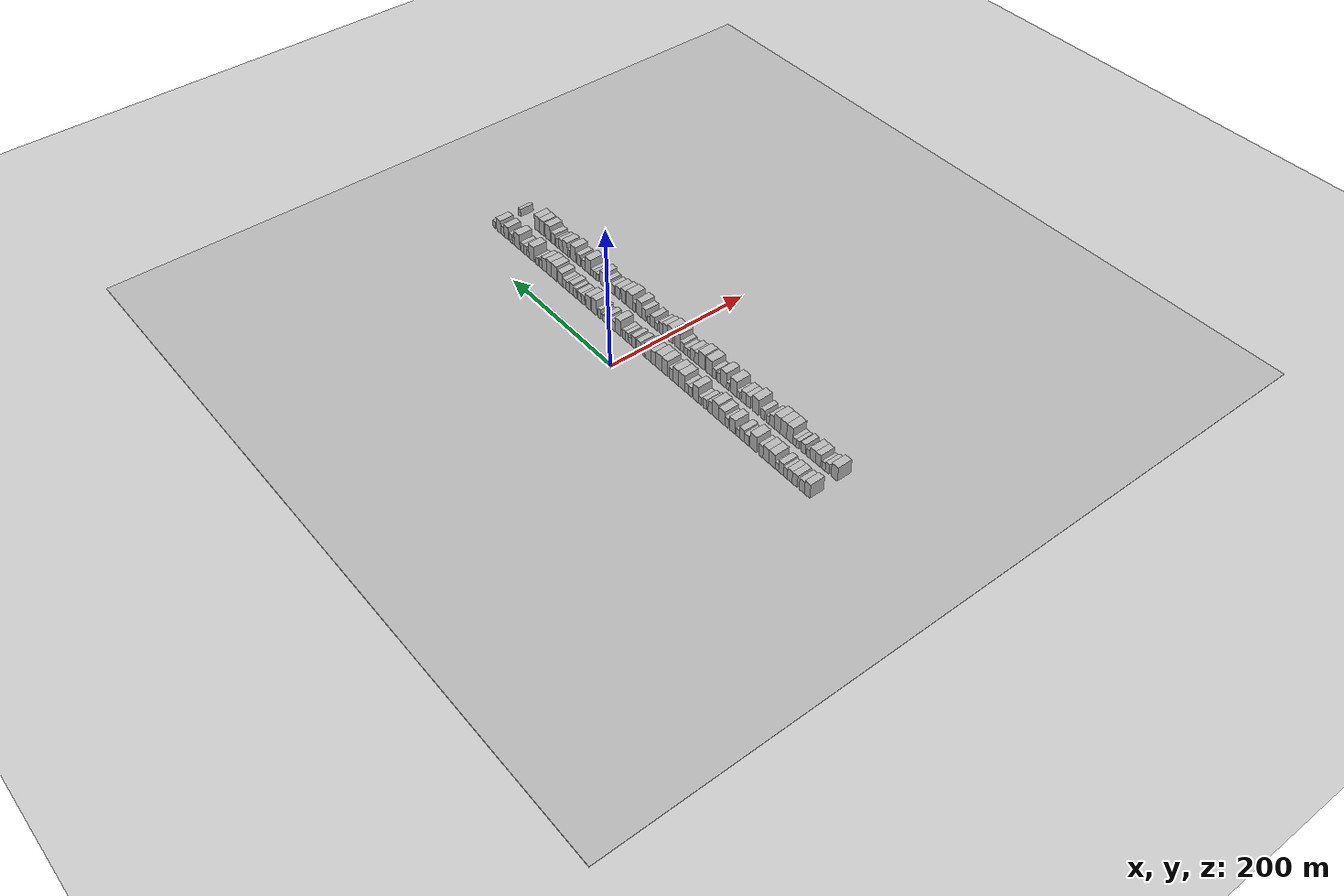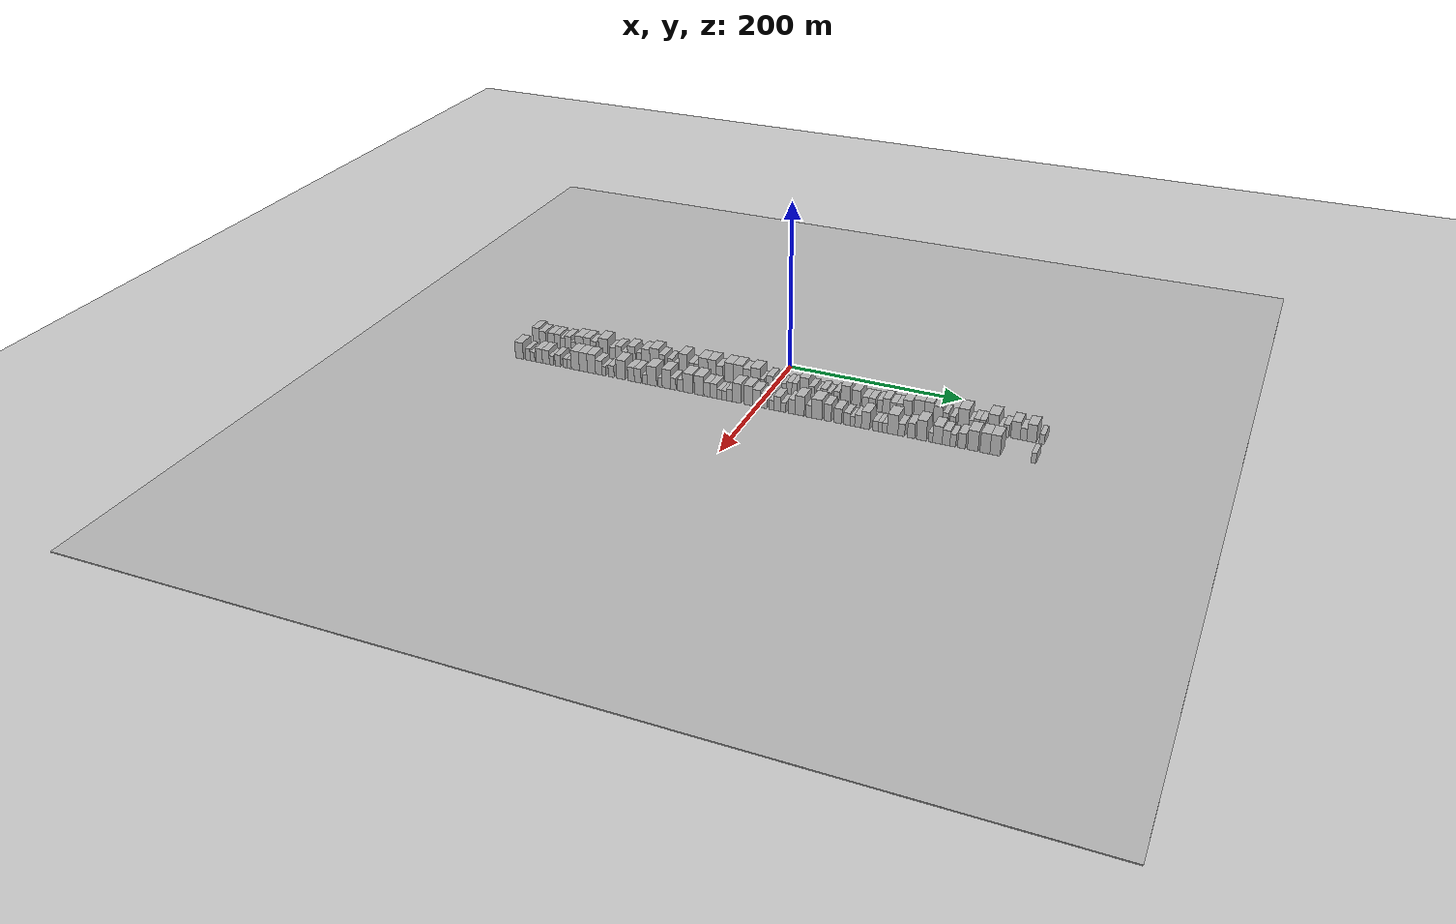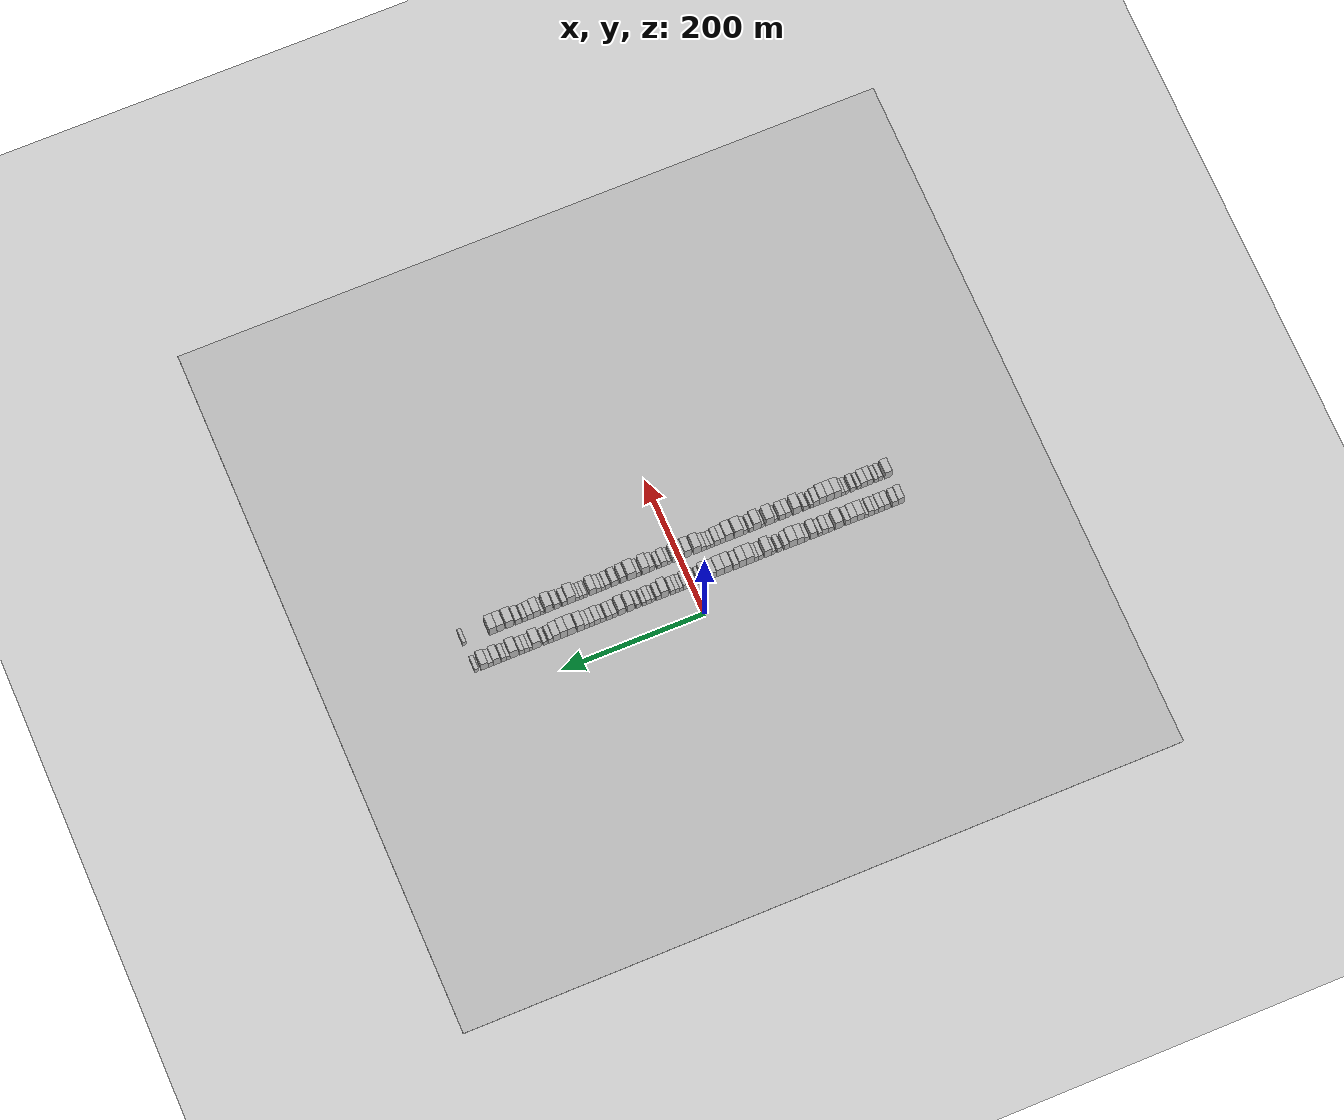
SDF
<?xml version="1.0" encoding="utf-8"?>

<sdf version="1.6">

   <world name="default">

      <gui fullscreen="0">

         <camera name="user_camera">

            <pose>-15 0 4.57585 0 0 0</pose>

            <view_controller>orbit</view_controller>

         </camera>

      </gui>

      <scene>

         <sky>

           <clouds>

             <speed>12</speed>

           </clouds>

         </sky>

         <ambient>0.4 0.4 0.4 1</ambient>

         <background>0.7 0.7 0.7 1</background>

         <shadows>1</shadows>

      </scene>

      <gravity>0 0 -9.8066</gravity>

      <magnetic_field>6e-06 2.3e-05 -4.2e-05</magnetic_field>

      <physics default="0" name="default_physics" type="ode">

         <ode>

            <solver>

               <type>quick</type>

               <iters>10</iters>

               <sor>1.0</sor>

               <use_dynamic_moi_rescaling>0</use_dynamic_moi_rescaling>

            </solver>

            <constraints>

               <cfm>0</cfm>

               <erp>0.2</erp>

               <contact_max_correcting_vel>100</contact_max_correcting_vel>

               <contact_surface_layer>0.001</contact_surface_layer>

            </constraints>

         </ode>

         <max_step_size>0.004</max_step_size>

         <real_time_factor>1</real_time_factor>

         <real_time_update_rate>250</real_time_update_rate>

      </physics>

      <light name="sun" type="directional">

         <cast_shadows>1</cast_shadows>

         <pose>0 0 10 0 0 0</pose>

         <diffuse>0.8 0.8 0.8 1</diffuse>

         <specular>0.2 0.2 0.2 1</specular>

         <attenuation>

            <range>1000</range>

            <constant>0.9</constant>

            <linear>0.01</linear>

            <quadratic>0.001</quadratic>

         </attenuation>

         <direction>-0.5 0.1 -0.9</direction>

      </light>

      <include>

         <name>ground_plane_1</name>

         <uri>model://HANNAS_ground_plane</uri>

         <pose>0 0 0  0 0 0</pose>

      </include>

      <include>

         <name>ground_plane_2</name>

         <uri>model://HANNAS_ground_plane</uri>

         <pose>100 0 0  0 0 0</pose>

      </include>

      <model name="building_1">

         <static>1</static>

         <pose frame="">50.0000 -295.6084 0 0.000000 0.000000 0.000000</pose>

         <link name="link">

            <pose frame="">0 0 10.50 0 0 0</pose>

            <collision name="collision">

               <geometry>

                  <box>

                     <size>20.0000 8.7832 21.0000</size>

                  </box>

               </geometry>

               <max_contacts>10</max_contacts>

               <surface>

                  <contact>

                     <ode/>

                  </contact>

                  <bounce/>

                  <friction>

                     <torsional>

                        <ode/>

                     </torsional>

                     <ode/>

                  </friction>

               </surface>

            </collision>

            <visual name="visual">

               <cast_shadows>0</cast_shadows>

               <geometry>

                  <box>

                     <size>20.0000 8.7832 21.0000</size>

                  </box>

               </geometry>

               <material>

                  <script>

                     <uri>model://HANNAS_wall/materials/scripts</uri>

                     <uri>model://HANNAS_wall/materials/textures</uri>

                     <name>vrc/HANNAS_wall</name>

                  </script>

               </material>

            </visual>

            <self_collide>0</self_collide>

            <enable_wind>0</enable_wind>

            <kinematic>0</kinematic>

         </link>

      </model>

      <model name="building_2">

         <static>1</static>

         <pose frame="">50.0000 -287.0106 0 0.000000 0.000000 0.000000</pose>

         <link name="link">

            <pose frame="">0 0 9.00 0 0 0</pose>

            <collision name="collision">

               <geometry>

                  <box>

                     <size>20.0000 8.4124 18.0000</size>

                  </box>

               </geometry>

               <max_contacts>10</max_contacts>

               <surface>

                  <contact>

                     <ode/>

                  </contact>

                  <bounce/>

                  <friction>

                     <torsional>

                        <ode/>

                     </torsional>

                     <ode/>

                  </friction>

               </surface>

            </collision>

            <visual name="visual">

               <cast_shadows>0</cast_shadows>

               <geometry>

                  <box>

                     <size>20.0000 8.4124 18.0000</size>

                  </box>

               </geometry>

               <material>

                  <script>

                     <uri>model://HANNAS_wall/materials/scripts</uri>

                     <uri>model://HANNAS_wall/materials/textures</uri>

                     <name>vrc/HANNAS_wall</name>

                  </script>

               </material>

            </visual>

            <self_collide>0</self_collide>

            <enable_wind>0</enable_wind>

            <kinematic>0</kinematic>

         </link>

      </model>

      <model name="building_3">

         <static>1</static>

         <pose frame="">50.0000 -275.5951 0 0.000000 0.000000 0.000000</pose>

         <link name="link">

            <pose frame="">0 0 9.00 0 0 0</pose>

            <collision name="collision">

               <geometry>

                  <box>

                     <size>20.0000 8.4186 18.0000</size>

                  </box>

               </geometry>

               <max_contacts>10</max_contacts>

               <surface>

                  <contact>

                     <ode/>

                  </contact>

                  <bounce/>

                  <friction>

                     <torsional>

                        <ode/>

                     </torsional>

                     <ode/>

                  </friction>

               </surface>

            </collision>

            <visual name="visual">

               <cast_shadows>0</cast_shadows>

               <geometry>

                  <box>

                     <size>20.0000 8.4186 18.0000</size>

                  </box>

               </geometry>

               <material>

                  <script>

                     <uri>model://HANNAS_wall/materials/scripts</uri>

                     <uri>model://HANNAS_wall/materials/textures</uri>

                     <name>vrc/HANNAS_wall</name>

                  </script>

               </material>

            </visual>

            <self_collide>0</self_collide>

            <enable_wind>0</enable_wind>

            <kinematic>0</kinematic>

         </link>

      </model>

      <model name="building_4">

         <static>1</static>

         <pose frame="">50.0000 -267.5192 0 0.000000 0.000000 0.000000</pose>

         <link name="link">

            <pose frame="">0 0 9.00 0 0 0</pose>

            <collision name="collision">

               <geometry>

                  <box>

                     <size>20.0000 7.7331 18.0000</size>

                  </box>

               </geometry>

               <max_contacts>10</max_contacts>

               <surface>

                  <contact>

                     <ode/>

                  </contact>

                  <bounce/>

                  <friction>

                     <torsional>

                        <ode/>

                     </torsional>

                     <ode/>

                  </friction>

               </surface>

            </collision>

            <visual name="visual">

               <cast_shadows>0</cast_shadows>

               <geometry>

                  <box>

                     <size>20.0000 7.7331 18.0000</size>

                  </box>

               </geometry>

               <material>

                  <script>

                     <uri>model://HANNAS_wall/materials/scripts</uri>

                     <uri>model://HANNAS_wall/materials/textures</uri>

                     <name>vrc/HANNAS_wall</name>

                  </script>

               </material>

            </visual>

            <self_collide>0</self_collide>

            <enable_wind>0</enable_wind>

            <kinematic>0</kinematic>

         </link>

      </model>

      <model name="building_5">

         <static>1</static>

         <pose frame="">50.0000 -260.5304 0 0.000000 0.000000 0.000000</pose>

         <link name="link">

            <pose frame="">0 0 7.50 0 0 0</pose>

            <collision name="collision">

               <geometry>

                  <box>

                     <size>20.0000 6.2446 15.0000</size>

                  </box>

               </geometry>

               <max_contacts>10</max_contacts>

               <surface>

                  <contact>

                     <ode/>

                  </contact>

                  <bounce/>

                  <friction>

                     <torsional>

                        <ode/>

                     </torsional>

                     <ode/>

                  </friction>

               </surface>

            </collision>

            <visual name="visual">

               <cast_shadows>0</cast_shadows>

               <geometry>

                  <box>

                     <size>20.0000 6.2446 15.0000</size>

                  </box>

               </geometry>

               <material>

                  <script>

                     <uri>model://HANNAS_wall/materials/scripts</uri>

                     <uri>model://HANNAS_wall/materials/textures</uri>

                     <name>vrc/HANNAS_wall</name>

                  </script>

               </material>

            </visual>

            <self_collide>0</self_collide>

            <enable_wind>0</enable_wind>

            <kinematic>0</kinematic>

         </link>

      </model>

      <model name="building_6">

         <static>1</static>

         <pose frame="">50.0000 -253.3990 0 0.000000 0.000000 0.000000</pose>

         <link name="link">

            <pose frame="">0 0 9.00 0 0 0</pose>

            <collision name="collision">

               <geometry>

                  <box>

                     <size>20.0000 8.0182 18.0000</size>

                  </box>

               </geometry>

               <max_contacts>10</max_contacts>

               <surface>

                  <contact>

                     <ode/>

                  </contact>

                  <bounce/>

                  <friction>

                     <torsional>

                        <ode/>

                     </torsional>

                     <ode/>

                  </friction>

               </surface>

            </collision>

            <visual name="visual">

               <cast_shadows>0</cast_shadows>

               <geometry>

                  <box>

                     <size>20.0000 8.0182 18.0000</size>

                  </box>

               </geometry>

               <material>

                  <script>

                     <uri>model://HANNAS_wall/materials/scripts</uri>

                     <uri>model://HANNAS_wall/materials/textures</uri>

                     <name>vrc/HANNAS_wall</name>

                  </script>

               </material>

            </visual>

            <self_collide>0</self_collide>

            <enable_wind>0</enable_wind>

            <kinematic>0</kinematic>

         </link>

      </model>

      <model name="building_7">

         <static>1</static>

         <pose frame="">50.0000 -246.5467 0 0.000000 0.000000 0.000000</pose>

         <link name="link">

            <pose frame="">0 0 6.00 0 0 0</pose>

            <collision name="collision">

               <geometry>

                  <box>

                     <size>20.0000 5.6864 12.0000</size>

                  </box>

               </geometry>

               <max_contacts>10</max_contacts>

               <surface>

                  <contact>

                     <ode/>

                  </contact>

                  <bounce/>

                  <friction>

                     <torsional>

                        <ode/>

                     </torsional>

                     <ode/>

                  </friction>

               </surface>

            </collision>

            <visual name="visual">

               <cast_shadows>0</cast_shadows>

               <geometry>

                  <box>

                     <size>20.0000 5.6864 12.0000</size>

                  </box>

               </geometry>

               <material>

                  <script>

                     <uri>model://HANNAS_wall/materials/scripts</uri>

                     <uri>model://HANNAS_wall/materials/textures</uri>

                     <name>vrc/HANNAS_wall</name>

                  </script>

               </material>

            </visual>

            <self_collide>0</self_collide>

            <enable_wind>0</enable_wind>

            <kinematic>0</kinematic>

         </link>

      </model>

      <model name="building_8">

         <static>1</static>

         <pose frame="">50.0000 -238.4841 0 0.000000 0.000000 0.000000</pose>

         <link name="link">

            <pose frame="">0 0 10.50 0 0 0</pose>

            <collision name="collision">

               <geometry>

                  <box>

                     <size>20.0000 10.4387 21.0000</size>

                  </box>

               </geometry>

               <max_contacts>10</max_contacts>

               <surface>

                  <contact>

                     <ode/>

                  </contact>

                  <bounce/>

                  <friction>

                     <torsional>

                        <ode/>

                     </torsional>

                     <ode/>

                  </friction>

               </surface>

            </collision>

            <visual name="visual">

               <cast_shadows>0</cast_shadows>

               <geometry>

                  <box>

                     <size>20.0000 10.4387 21.0000</size>

                  </box>

               </geometry>

               <material>

                  <script>

                     <uri>model://HANNAS_wall/materials/scripts</uri>

                     <uri>model://HANNAS_wall/materials/textures</uri>

                     <name>vrc/HANNAS_wall</name>

                  </script>

               </material>

            </visual>

            <self_collide>0</self_collide>

            <enable_wind>0</enable_wind>

            <kinematic>0</kinematic>

         </link>

      </model>

      <model name="building_9">

         <static>1</static>

         <pose frame="">50.0000 -228.4582 0 0.000000 0.000000 0.000000</pose>

         <link name="link">

            <pose frame="">0 0 10.50 0 0 0</pose>

            <collision name="collision">

               <geometry>

                  <box>

                     <size>20.0000 9.6133 21.0000</size>

                  </box>

               </geometry>

               <max_contacts>10</max_contacts>

               <surface>

                  <contact>

                     <ode/>

                  </contact>

                  <bounce/>

                  <friction>

                     <torsional>

                        <ode/>

                     </torsional>

                     <ode/>

                  </friction>

               </surface>

            </collision>

            <visual name="visual">

               <cast_shadows>0</cast_shadows>

               <geometry>

                  <box>

                     <size>20.0000 9.6133 21.0000</size>

                  </box>

               </geometry>

               <material>

                  <script>

                     <uri>model://HANNAS_wall/materials/scripts</uri>

                     <uri>model://HANNAS_wall/materials/textures</uri>

                     <name>vrc/HANNAS_wall</name>

                  </script>

               </material>

            </visual>

            <self_collide>0</self_collide>

            <enable_wind>0</enable_wind>

            <kinematic>0</kinematic>

         </link>

      </model>

      <model name="building_10">

         <static>1</static>

         <pose frame="">50.0000 -219.9443 0 0.000000 0.000000 0.000000</pose>

         <link name="link">

            <pose frame="">0 0 9.00 0 0 0</pose>

            <collision name="collision">

               <geometry>

                  <box>

                     <size>20.0000 7.4143 18.0000</size>

                  </box>

               </geometry>

               <max_contacts>10</max_contacts>

               <surface>

                  <contact>

                     <ode/>

                  </contact>

                  <bounce/>

                  <friction>

                     <torsional>

                        <ode/>

                     </torsional>

                     <ode/>

                  </friction>

               </surface>

            </collision>

            <visual name="visual">

               <cast_shadows>0</cast_shadows>

               <geometry>

                  <box>

                     <size>20.0000 7.4143 18.0000</size>

                  </box>

               </geometry>

               <material>

                  <script>

                     <uri>model://HANNAS_wall/materials/scripts</uri>

                     <uri>model://HANNAS_wall/materials/textures</uri>

                     <name>vrc/HANNAS_wall</name>

                  </script>

               </material>

            </visual>

            <self_collide>0</self_collide>

            <enable_wind>0</enable_wind>

            <kinematic>0</kinematic>

         </link>

      </model>

      <model name="building_11">

         <static>1</static>

         <pose frame="">50.0000 -207.4244 0 0.000000 0.000000 0.000000</pose>

         <link name="link">

            <pose frame="">0 0 12.00 0 0 0</pose>

            <collision name="collision">

               <geometry>

                  <box>

                     <size>20.0000 11.6256 24.0000</size>

                  </box>

               </geometry>

               <max_contacts>10</max_contacts>

               <surface>

                  <contact>

                     <ode/>

                  </contact>

                  <bounce/>

                  <friction>

                     <torsional>

                        <ode/>

                     </torsional>

                     <ode/>

                  </friction>

               </surface>

            </collision>

            <visual name="visual">

               <cast_shadows>0</cast_shadows>

               <geometry>

                  <box>

                     <size>20.0000 11.6256 24.0000</size>

                  </box>

               </geometry>

               <material>

                  <script>

                     <uri>model://HANNAS_wall/materials/scripts</uri>

                     <uri>model://HANNAS_wall/materials/textures</uri>

                     <name>vrc/HANNAS_wall</name>

                  </script>

               </material>

            </visual>

            <self_collide>0</self_collide>

            <enable_wind>0</enable_wind>

            <kinematic>0</kinematic>

         </link>

      </model>

      <model name="building_12">

         <static>1</static>

         <pose frame="">50.0000 -195.9075 0 0.000000 0.000000 0.000000</pose>

         <link name="link">

            <pose frame="">0 0 7.50 0 0 0</pose>

            <collision name="collision">

               <geometry>

                  <box>

                     <size>20.0000 7.4081 15.0000</size>

                  </box>

               </geometry>

               <max_contacts>10</max_contacts>

               <surface>

                  <contact>

                     <ode/>

                  </contact>

                  <bounce/>

                  <friction>

                     <torsional>

                        <ode/>

                     </torsional>

                     <ode/>

                  </friction>

               </surface>

            </collision>

            <visual name="visual">

               <cast_shadows>0</cast_shadows>

               <geometry>

                  <box>

                     <size>20.0000 7.4081 15.0000</size>

                  </box>

               </geometry>

               <material>

                  <script>

                     <uri>model://HANNAS_wall/materials/scripts</uri>

                     <uri>model://HANNAS_wall/materials/textures</uri>

                     <name>vrc/HANNAS_wall</name>

                  </script>

               </material>

            </visual>

            <self_collide>0</self_collide>

            <enable_wind>0</enable_wind>

            <kinematic>0</kinematic>

         </link>

      </model>

      <model name="building_13">

         <static>1</static>

         <pose frame="">50.0000 -188.0218 0 0.000000 0.000000 0.000000</pose>

         <link name="link">

            <pose frame="">0 0 9.00 0 0 0</pose>

            <collision name="collision">

               <geometry>

                  <box>

                     <size>20.0000 8.3633 18.0000</size>

                  </box>

               </geometry>

               <max_contacts>10</max_contacts>

               <surface>

                  <contact>

                     <ode/>

                  </contact>

                  <bounce/>

                  <friction>

                     <torsional>

                        <ode/>

                     </torsional>

                     <ode/>

                  </friction>

               </surface>

            </collision>

            <visual name="visual">

               <cast_shadows>0</cast_shadows>

               <geometry>

                  <box>

                     <size>20.0000 8.3633 18.0000</size>

                  </box>

               </geometry>

               <material>

                  <script>

                     <uri>model://HANNAS_wall/materials/scripts</uri>

                     <uri>model://HANNAS_wall/materials/textures</uri>

                     <name>vrc/HANNAS_wall</name>

                  </script>

               </material>

            </visual>

            <self_collide>0</self_collide>

            <enable_wind>0</enable_wind>

            <kinematic>0</kinematic>

         </link>

      </model>

      <model name="building_14">

         <static>1</static>

         <pose frame="">50.0000 -181.0776 0 0.000000 0.000000 0.000000</pose>

         <link name="link">

            <pose frame="">0 0 6.00 0 0 0</pose>

            <collision name="collision">

               <geometry>

                  <box>

                     <size>20.0000 5.5251 12.0000</size>

                  </box>

               </geometry>

               <max_contacts>10</max_contacts>

               <surface>

                  <contact>

                     <ode/>

                  </contact>

                  <bounce/>

                  <friction>

                     <torsional>

                        <ode/>

                     </torsional>

                     <ode/>

                  </friction>

               </surface>

            </collision>

            <visual name="visual">

               <cast_shadows>0</cast_shadows>

               <geometry>

                  <box>

                     <size>20.0000 5.5251 12.0000</size>

                  </box>

               </geometry>

               <material>

                  <script>

                     <uri>model://HANNAS_wall/materials/scripts</uri>

                     <uri>model://HANNAS_wall/materials/textures</uri>

                     <name>vrc/HANNAS_wall</name>

                  </script>

               </material>

            </visual>

            <self_collide>0</self_collide>

            <enable_wind>0</enable_wind>

            <kinematic>0</kinematic>

         </link>

      </model>

      <model name="building_15">

         <static>1</static>

         <pose frame="">50.0000 -171.4688 0 0.000000 0.000000 0.000000</pose>

         <link name="link">

            <pose frame="">0 0 10.50 0 0 0</pose>

            <collision name="collision">

               <geometry>

                  <box>

                     <size>20.0000 9.6924 21.0000</size>

                  </box>

               </geometry>

               <max_contacts>10</max_contacts>

               <surface>

                  <contact>

                     <ode/>

                  </contact>

                  <bounce/>

                  <friction>

                     <torsional>

                        <ode/>

                     </torsional>

                     <ode/>

                  </friction>

               </surface>

            </collision>

            <visual name="visual">

               <cast_shadows>0</cast_shadows>

               <geometry>

                  <box>

                     <size>20.0000 9.6924 21.0000</size>

                  </box>

               </geometry>

               <material>

                  <script>

                     <uri>model://HANNAS_wall/materials/scripts</uri>

                     <uri>model://HANNAS_wall/materials/textures</uri>

                     <name>vrc/HANNAS_wall</name>

                  </script>

               </material>

            </visual>

            <self_collide>0</self_collide>

            <enable_wind>0</enable_wind>

            <kinematic>0</kinematic>

         </link>

      </model>

      <model name="building_16">

         <static>1</static>

         <pose frame="">50.0000 -161.5749 0 0.000000 0.000000 0.000000</pose>

         <link name="link">

            <pose frame="">0 0 7.50 0 0 0</pose>

            <collision name="collision">

               <geometry>

                  <box>

                     <size>20.0000 6.0954 15.0000</size>

                  </box>

               </geometry>

               <max_contacts>10</max_contacts>

               <surface>

                  <contact>

                     <ode/>

                  </contact>

                  <bounce/>

                  <friction>

                     <torsional>

                        <ode/>

                     </torsional>

                     <ode/>

                  </friction>

               </surface>

            </collision>

            <visual name="visual">

               <cast_shadows>0</cast_shadows>

               <geometry>

                  <box>

                     <size>20.0000 6.0954 15.0000</size>

                  </box>

               </geometry>

               <material>

                  <script>

                     <uri>model://HANNAS_wall/materials/scripts</uri>

                     <uri>model://HANNAS_wall/materials/textures</uri>

                     <name>vrc/HANNAS_wall</name>

                  </script>

               </material>

            </visual>

            <self_collide>0</self_collide>

            <enable_wind>0</enable_wind>

            <kinematic>0</kinematic>

         </link>

      </model>

      <model name="building_17">

         <static>1</static>

         <pose frame="">50.0000 -153.3585 0 0.000000 0.000000 0.000000</pose>

         <link name="link">

            <pose frame="">0 0 10.50 0 0 0</pose>

            <collision name="collision">

               <geometry>

                  <box>

                     <size>20.0000 10.3374 21.0000</size>

                  </box>

               </geometry>

               <max_contacts>10</max_contacts>

               <surface>

                  <contact>

                     <ode/>

                  </contact>

                  <bounce/>

                  <friction>

                     <torsional>

                        <ode/>

                     </torsional>

                     <ode/>

                  </friction>

               </surface>

            </collision>

            <visual name="visual">

               <cast_shadows>0</cast_shadows>

               <geometry>

                  <box>

                     <size>20.0000 10.3374 21.0000</size>

                  </box>

               </geometry>

               <material>

                  <script>

                     <uri>model://HANNAS_wall/materials/scripts</uri>

                     <uri>model://HANNAS_wall/materials/textures</uri>

                     <name>vrc/HANNAS_wall</name>

                  </script>

               </material>

            </visual>

            <self_collide>0</self_collide>

            <enable_wind>0</enable_wind>

            <kinematic>0</kinematic>

         </link>

      </model>

      <model name="building_18">

         <static>1</static>

         <pose frame="">50.0000 -142.4200 0 0.000000 0.000000 0.000000</pose>

         <link name="link">

            <pose frame="">0 0 12.00 0 0 0</pose>

            <collision name="collision">

               <geometry>

                  <box>

                     <size>20.0000 11.5396 24.0000</size>

                  </box>

               </geometry>

               <max_contacts>10</max_contacts>

               <surface>

                  <contact>

                     <ode/>

                  </contact>

                  <bounce/>

                  <friction>

                     <torsional>

                        <ode/>

                     </torsional>

                     <ode/>

                  </friction>

               </surface>

            </collision>

            <visual name="visual">

               <cast_shadows>0</cast_shadows>

               <geometry>

                  <box>

                     <size>20.0000 11.5396 24.0000</size>

                  </box>

               </geometry>

               <material>

                  <script>

                     <uri>model://HANNAS_wall/materials/scripts</uri>

                     <uri>model://HANNAS_wall/materials/textures</uri>

                     <name>vrc/HANNAS_wall</name>

                  </script>

               </material>

            </visual>

            <self_collide>0</self_collide>

            <enable_wind>0</enable_wind>

            <kinematic>0</kinematic>

         </link>

      </model>

      <model name="building_19">

         <static>1</static>

         <pose frame="">50.0000 -132.9575 0 0.000000 0.000000 0.000000</pose>

         <link name="link">

            <pose frame="">0 0 9.00 0 0 0</pose>

            <collision name="collision">

               <geometry>

                  <box>

                     <size>20.0000 7.3854 18.0000</size>

                  </box>

               </geometry>

               <max_contacts>10</max_contacts>

               <surface>

                  <contact>

                     <ode/>

                  </contact>

                  <bounce/>

                  <friction>

                     <torsional>

                        <ode/>

                     </torsional>

                     <ode/>

                  </friction>

               </surface>

            </collision>

            <visual name="visual">

               <cast_shadows>0</cast_shadows>

               <geometry>

                  <box>

                     <size>20.0000 7.3854 18.0000</size>

                  </box>

               </geometry>

               <material>

                  <script>

                     <uri>model://HANNAS_wall/materials/scripts</uri>

                     <uri>model://HANNAS_wall/materials/textures</uri>

                     <name>vrc/HANNAS_wall</name>

                  </script>

               </material>

            </visual>

            <self_collide>0</self_collide>

            <enable_wind>0</enable_wind>

            <kinematic>0</kinematic>

         </link>

      </model>

      <model name="building_20">

         <static>1</static>

         <pose frame="">50.0000 -123.0354 0 0.000000 0.000000 0.000000</pose>

         <link name="link">

            <pose frame="">0 0 7.50 0 0 0</pose>

            <collision name="collision">

               <geometry>

                  <box>

                     <size>20.0000 6.4587 15.0000</size>

                  </box>

               </geometry>

               <max_contacts>10</max_contacts>

               <surface>

                  <contact>

                     <ode/>

                  </contact>

                  <bounce/>

                  <friction>

                     <torsional>

                        <ode/>

                     </torsional>

                     <ode/>

                  </friction>

               </surface>

            </collision>

            <visual name="visual">

               <cast_shadows>0</cast_shadows>

               <geometry>

                  <box>

                     <size>20.0000 6.4587 15.0000</size>

                  </box>

               </geometry>

               <material>

                  <script>

                     <uri>model://HANNAS_wall/materials/scripts</uri>

                     <uri>model://HANNAS_wall/materials/textures</uri>

                     <name>vrc/HANNAS_wall</name>

                  </script>

               </material>

            </visual>

            <self_collide>0</self_collide>

            <enable_wind>0</enable_wind>

            <kinematic>0</kinematic>

         </link>

      </model>

      <model name="building_21">

         <static>1</static>

         <pose frame="">50.0000 -114.9029 0 0.000000 0.000000 0.000000</pose>

         <link name="link">

            <pose frame="">0 0 6.00 0 0 0</pose>

            <collision name="collision">

               <geometry>

                  <box>

                     <size>20.0000 5.8064 12.0000</size>

                  </box>

               </geometry>

               <max_contacts>10</max_contacts>

               <surface>

                  <contact>

                     <ode/>

                  </contact>

                  <bounce/>

                  <friction>

                     <torsional>

                        <ode/>

                     </torsional>

                     <ode/>

                  </friction>

               </surface>

            </collision>

            <visual name="visual">

               <cast_shadows>0</cast_shadows>

               <geometry>

                  <box>

                     <size>20.0000 5.8064 12.0000</size>

                  </box>

               </geometry>

               <material>

                  <script>

                     <uri>model://HANNAS_wall/materials/scripts</uri>

                     <uri>model://HANNAS_wall/materials/textures</uri>

                     <name>vrc/HANNAS_wall</name>

                  </script>

               </material>

            </visual>

            <self_collide>0</self_collide>

            <enable_wind>0</enable_wind>

            <kinematic>0</kinematic>

         </link>

      </model>

      <model name="building_22">

         <static>1</static>

         <pose frame="">50.0000 -106.9604 0 0.000000 0.000000 0.000000</pose>

         <link name="link">

            <pose frame="">0 0 12.00 0 0 0</pose>

            <collision name="collision">

               <geometry>

                  <box>

                     <size>20.0000 10.0785 24.0000</size>

                  </box>

               </geometry>

               <max_contacts>10</max_contacts>

               <surface>

                  <contact>

                     <ode/>

                  </contact>

                  <bounce/>

                  <friction>

                     <torsional>

                        <ode/>

                     </torsional>

                     <ode/>

                  </friction>

               </surface>

            </collision>

            <visual name="visual">

               <cast_shadows>0</cast_shadows>

               <geometry>

                  <box>

                     <size>20.0000 10.0785 24.0000</size>

                  </box>

               </geometry>

               <material>

                  <script>

                     <uri>model://HANNAS_wall/materials/scripts</uri>

                     <uri>model://HANNAS_wall/materials/textures</uri>

                     <name>vrc/HANNAS_wall</name>

                  </script>

               </material>

            </visual>

            <self_collide>0</self_collide>

            <enable_wind>0</enable_wind>

            <kinematic>0</kinematic>

         </link>

      </model>

      <model name="building_23">

         <static>1</static>

         <pose frame="">50.0000 -96.7455 0 0.000000 0.000000 0.000000</pose>

         <link name="link">

            <pose frame="">0 0 7.50 0 0 0</pose>

            <collision name="collision">

               <geometry>

                  <box>

                     <size>20.0000 6.3514 15.0000</size>

                  </box>

               </geometry>

               <max_contacts>10</max_contacts>

               <surface>

                  <contact>

                     <ode/>

                  </contact>

                  <bounce/>

                  <friction>

                     <torsional>

                        <ode/>

                     </torsional>

                     <ode/>

                  </friction>

               </surface>

            </collision>

            <visual name="visual">

               <cast_shadows>0</cast_shadows>

               <geometry>

                  <box>

                     <size>20.0000 6.3514 15.0000</size>

                  </box>

               </geometry>

               <material>

                  <script>

                     <uri>model://HANNAS_wall/materials/scripts</uri>

                     <uri>model://HANNAS_wall/materials/textures</uri>

                     <name>vrc/HANNAS_wall</name>

                  </script>

               </material>

            </visual>

            <self_collide>0</self_collide>

            <enable_wind>0</enable_wind>

            <kinematic>0</kinematic>

         </link>

      </model>

      <model name="building_24">

         <static>1</static>

         <pose frame="">50.0000 -90.5376 0 0.000000 0.000000 0.000000</pose>

         <link name="link">

            <pose frame="">0 0 7.50 0 0 0</pose>

            <collision name="collision">

               <geometry>

                  <box>

                     <size>20.0000 6.0643 15.0000</size>

                  </box>

               </geometry>

               <max_contacts>10</max_contacts>

               <surface>

                  <contact>

                     <ode/>

                  </contact>

                  <bounce/>

                  <friction>

                     <torsional>

                        <ode/>

                     </torsional>

                     <ode/>

                  </friction>

               </surface>

            </collision>

            <visual name="visual">

               <cast_shadows>0</cast_shadows>

               <geometry>

                  <box>

                     <size>20.0000 6.0643 15.0000</size>

                  </box>

               </geometry>

               <material>

                  <script>

                     <uri>model://HANNAS_wall/materials/scripts</uri>

                     <uri>model://HANNAS_wall/materials/textures</uri>

                     <name>vrc/HANNAS_wall</name>

                  </script>

               </material>

            </visual>

            <self_collide>0</self_collide>

            <enable_wind>0</enable_wind>

            <kinematic>0</kinematic>

         </link>

      </model>

      <model name="building_25">

         <static>1</static>

         <pose frame="">50.0000 -81.9061 0 0.000000 0.000000 0.000000</pose>

         <link name="link">

            <pose frame="">0 0 12.00 0 0 0</pose>

            <collision name="collision">

               <geometry>

                  <box>

                     <size>20.0000 11.1988 24.0000</size>

                  </box>

               </geometry>

               <max_contacts>10</max_contacts>

               <surface>

                  <contact>

                     <ode/>

                  </contact>

                  <bounce/>

                  <friction>

                     <torsional>

                        <ode/>

                     </torsional>

                     <ode/>

                  </friction>

               </surface>

            </collision>

            <visual name="visual">

               <cast_shadows>0</cast_shadows>

               <geometry>

                  <box>

                     <size>20.0000 11.1988 24.0000</size>

                  </box>

               </geometry>

               <material>

                  <script>

                     <uri>model://HANNAS_wall/materials/scripts</uri>

                     <uri>model://HANNAS_wall/materials/textures</uri>

                     <name>vrc/HANNAS_wall</name>

                  </script>

               </material>

            </visual>

            <self_collide>0</self_collide>

            <enable_wind>0</enable_wind>

            <kinematic>0</kinematic>

         </link>

      </model>

      <model name="building_26">

         <static>1</static>

         <pose frame="">50.0000 -71.0972 0 0.000000 0.000000 0.000000</pose>

         <link name="link">

            <pose frame="">0 0 12.00 0 0 0</pose>

            <collision name="collision">

               <geometry>

                  <box>

                     <size>20.0000 10.4188 24.0000</size>

                  </box>

               </geometry>

               <max_contacts>10</max_contacts>

               <surface>

                  <contact>

                     <ode/>

                  </contact>

                  <bounce/>

                  <friction>

                     <torsional>

                        <ode/>

                     </torsional>

                     <ode/>

                  </friction>

               </surface>

            </collision>

            <visual name="visual">

               <cast_shadows>0</cast_shadows>

               <geometry>

                  <box>

                     <size>20.0000 10.4188 24.0000</size>

                  </box>

               </geometry>

               <material>

                  <script>

                     <uri>model://HANNAS_wall/materials/scripts</uri>

                     <uri>model://HANNAS_wall/materials/textures</uri>

                     <name>vrc/HANNAS_wall</name>

                  </script>

               </material>

            </visual>

            <self_collide>0</self_collide>

            <enable_wind>0</enable_wind>

            <kinematic>0</kinematic>

         </link>

      </model>

      <model name="building_27">

         <static>1</static>

         <pose frame="">50.0000 -62.0028 0 0.000000 0.000000 0.000000</pose>

         <link name="link">

            <pose frame="">0 0 9.00 0 0 0</pose>

            <collision name="collision">

               <geometry>

                  <box>

                     <size>20.0000 7.7700 18.0000</size>

                  </box>

               </geometry>

               <max_contacts>10</max_contacts>

               <surface>

                  <contact>

                     <ode/>

                  </contact>

                  <bounce/>

                  <friction>

                     <torsional>

                        <ode/>

                     </torsional>

                     <ode/>

                  </friction>

               </surface>

            </collision>

            <visual name="visual">

               <cast_shadows>0</cast_shadows>

               <geometry>

                  <box>

                     <size>20.0000 7.7700 18.0000</size>

                  </box>

               </geometry>

               <material>

                  <script>

                     <uri>model://HANNAS_wall/materials/scripts</uri>

                     <uri>model://HANNAS_wall/materials/textures</uri>

                     <name>vrc/HANNAS_wall</name>

                  </script>

               </material>

            </visual>

            <self_collide>0</self_collide>

            <enable_wind>0</enable_wind>

            <kinematic>0</kinematic>

         </link>

      </model>

      <model name="building_28">

         <static>1</static>

         <pose frame="">50.0000 -50.7396 0 0.000000 0.000000 0.000000</pose>

         <link name="link">

            <pose frame="">0 0 12.00 0 0 0</pose>

            <collision name="collision">

               <geometry>

                  <box>

                     <size>20.0000 10.7563 24.0000</size>

                  </box>

               </geometry>

               <max_contacts>10</max_contacts>

               <surface>

                  <contact>

                     <ode/>

                  </contact>

                  <bounce/>

                  <friction>

                     <torsional>

                        <ode/>

                     </torsional>

                     <ode/>

                  </friction>

               </surface>

            </collision>

            <visual name="visual">

               <cast_shadows>0</cast_shadows>

               <geometry>

                  <box>

                     <size>20.0000 10.7563 24.0000</size>

                  </box>

               </geometry>

               <material>

                  <script>

                     <uri>model://HANNAS_wall/materials/scripts</uri>

                     <uri>model://HANNAS_wall/materials/textures</uri>

                     <name>vrc/HANNAS_wall</name>

                  </script>

               </material>

            </visual>

            <self_collide>0</self_collide>

            <enable_wind>0</enable_wind>

            <kinematic>0</kinematic>

         </link>

      </model>

      <model name="building_29">

         <static>1</static>

         <pose frame="">50.0000 -39.6867 0 0.000000 0.000000 0.000000</pose>

         <link name="link">

            <pose frame="">0 0 12.00 0 0 0</pose>

            <collision name="collision">

               <geometry>

                  <box>

                     <size>20.0000 11.3496 24.0000</size>

                  </box>

               </geometry>

               <max_contacts>10</max_contacts>

               <surface>

                  <contact>

                     <ode/>

                  </contact>

                  <bounce/>

                  <friction>

                     <torsional>

                        <ode/>

                     </torsional>

                     <ode/>

                  </friction>

               </surface>

            </collision>

            <visual name="visual">

               <cast_shadows>0</cast_shadows>

               <geometry>

                  <box>

                     <size>20.0000 11.3496 24.0000</size>

                  </box>

               </geometry>

               <material>

                  <script>

                     <uri>model://HANNAS_wall/materials/scripts</uri>

                     <uri>model://HANNAS_wall/materials/textures</uri>

                     <name>vrc/HANNAS_wall</name>

                  </script>

               </material>

            </visual>

            <self_collide>0</self_collide>

            <enable_wind>0</enable_wind>

            <kinematic>0</kinematic>

         </link>

      </model>

      <model name="building_30">

         <static>1</static>

         <pose frame="">50.0000 -29.3589 0 0.000000 0.000000 0.000000</pose>

         <link name="link">

            <pose frame="">0 0 10.50 0 0 0</pose>

            <collision name="collision">

               <geometry>

                  <box>

                     <size>20.0000 9.3060 21.0000</size>

                  </box>

               </geometry>

               <max_contacts>10</max_contacts>

               <surface>

                  <contact>

                     <ode/>

                  </contact>

                  <bounce/>

                  <friction>

                     <torsional>

                        <ode/>

                     </torsional>

                     <ode/>

                  </friction>

               </surface>

            </collision>

            <visual name="visual">

               <cast_shadows>0</cast_shadows>

               <geometry>

                  <box>

                     <size>20.0000 9.3060 21.0000</size>

                  </box>

               </geometry>

               <material>

                  <script>

                     <uri>model://HANNAS_wall/materials/scripts</uri>

                     <uri>model://HANNAS_wall/materials/textures</uri>

                     <name>vrc/HANNAS_wall</name>

                  </script>

               </material>

            </visual>

            <self_collide>0</self_collide>

            <enable_wind>0</enable_wind>

            <kinematic>0</kinematic>

         </link>

      </model>

      <model name="building_31">

         <static>1</static>

         <pose frame="">50.0000 -19.0063 0 0.000000 0.000000 0.000000</pose>

         <link name="link">

            <pose frame="">0 0 12.00 0 0 0</pose>

            <collision name="collision">

               <geometry>

                  <box>

                     <size>20.0000 11.3990 24.0000</size>

                  </box>

               </geometry>

               <max_contacts>10</max_contacts>

               <surface>

                  <contact>

                     <ode/>

                  </contact>

                  <bounce/>

                  <friction>

                     <torsional>

                        <ode/>

                     </torsional>

                     <ode/>

                  </friction>

               </surface>

            </collision>

            <visual name="visual">

               <cast_shadows>0</cast_shadows>

               <geometry>

                  <box>

                     <size>20.0000 11.3990 24.0000</size>

                  </box>

               </geometry>

               <material>

                  <script>

                     <uri>model://HANNAS_wall/materials/scripts</uri>

                     <uri>model://HANNAS_wall/materials/textures</uri>

                     <name>vrc/HANNAS_wall</name>

                  </script>

               </material>

            </visual>

            <self_collide>0</self_collide>

            <enable_wind>0</enable_wind>

            <kinematic>0</kinematic>

         </link>

      </model>

      <model name="building_32">

         <static>1</static>

         <pose frame="">50.0000 -10.8610 0 0.000000 0.000000 0.000000</pose>

         <link name="link">

            <pose frame="">0 0 6.00 0 0 0</pose>

            <collision name="collision">

               <geometry>

                  <box>

                     <size>20.0000 4.8917 12.0000</size>

                  </box>

               </geometry>

               <max_contacts>10</max_contacts>

               <surface>

                  <contact>

                     <ode/>

                  </contact>

                  <bounce/>

                  <friction>

                     <torsional>

                        <ode/>

                     </torsional>

                     <ode/>

                  </friction>

               </surface>

            </collision>

            <visual name="visual">

               <cast_shadows>0</cast_shadows>

               <geometry>

                  <box>

                     <size>20.0000 4.8917 12.0000</size>

                  </box>

               </geometry>

               <material>

                  <script>

                     <uri>model://HANNAS_wall/materials/scripts</uri>

                     <uri>model://HANNAS_wall/materials/textures</uri>

                     <name>vrc/HANNAS_wall</name>

                  </script>

               </material>

            </visual>

            <self_collide>0</self_collide>

            <enable_wind>0</enable_wind>

            <kinematic>0</kinematic>

         </link>

      </model>

      <model name="building_33">

         <static>1</static>

         <pose frame="">50.0000 -1.4541 0 0.000000 0.000000 0.000000</pose>

         <link name="link">

            <pose frame="">0 0 9.00 0 0 0</pose>

            <collision name="collision">

               <geometry>

                  <box>

                     <size>20.0000 7.9220 18.0000</size>

                  </box>

               </geometry>

               <max_contacts>10</max_contacts>

               <surface>

                  <contact>

                     <ode/>

                  </contact>

                  <bounce/>

                  <friction>

                     <torsional>

                        <ode/>

                     </torsional>

                     <ode/>

                  </friction>

               </surface>

            </collision>

            <visual name="visual">

               <cast_shadows>0</cast_shadows>

               <geometry>

                  <box>

                     <size>20.0000 7.9220 18.0000</size>

                  </box>

               </geometry>

               <material>

                  <script>

                     <uri>model://HANNAS_wall/materials/scripts</uri>

                     <uri>model://HANNAS_wall/materials/textures</uri>

                     <name>vrc/HANNAS_wall</name>

                  </script>

               </material>

            </visual>

            <self_collide>0</self_collide>

            <enable_wind>0</enable_wind>

            <kinematic>0</kinematic>

         </link>

      </model>

      <model name="building_34">

         <static>1</static>

         <pose frame="">50.0000 9.1386 0 0.000000 0.000000 0.000000</pose>

         <link name="link">

            <pose frame="">0 0 9.00 0 0 0</pose>

            <collision name="collision">

               <geometry>

                  <box>

                     <size>20.0000 7.2633 18.0000</size>

                  </box>

               </geometry>

               <max_contacts>10</max_contacts>

               <surface>

                  <contact>

                     <ode/>

                  </contact>

                  <bounce/>

                  <friction>

                     <torsional>

                        <ode/>

                     </torsional>

                     <ode/>

                  </friction>

               </surface>

            </collision>

            <visual name="visual">

               <cast_shadows>0</cast_shadows>

               <geometry>

                  <box>

                     <size>20.0000 7.2633 18.0000</size>

                  </box>

               </geometry>

               <material>

                  <script>

                     <uri>model://HANNAS_wall/materials/scripts</uri>

                     <uri>model://HANNAS_wall/materials/textures</uri>

                     <name>vrc/HANNAS_wall</name>

                  </script>

               </material>

            </visual>

            <self_collide>0</self_collide>

            <enable_wind>0</enable_wind>

            <kinematic>0</kinematic>

         </link>

      </model>

      <model name="building_35">

         <static>1</static>

         <pose frame="">50.0000 15.5627 0 0.000000 0.000000 0.000000</pose>

         <link name="link">

            <pose frame="">0 0 6.00 0 0 0</pose>

            <collision name="collision">

               <geometry>

                  <box>

                     <size>20.0000 5.5849 12.0000</size>

                  </box>

               </geometry>

               <max_contacts>10</max_contacts>

               <surface>

                  <contact>

                     <ode/>

                  </contact>

                  <bounce/>

                  <friction>

                     <torsional>

                        <ode/>

                     </torsional>

                     <ode/>

                  </friction>

               </surface>

            </collision>

            <visual name="visual">

               <cast_shadows>0</cast_shadows>

               <geometry>

                  <box>

                     <size>20.0000 5.5849 12.0000</size>

                  </box>

               </geometry>

               <material>

                  <script>

                     <uri>model://HANNAS_wall/materials/scripts</uri>

                     <uri>model://HANNAS_wall/materials/textures</uri>

                     <name>vrc/HANNAS_wall</name>

                  </script>

               </material>

            </visual>

            <self_collide>0</self_collide>

            <enable_wind>0</enable_wind>

            <kinematic>0</kinematic>

         </link>

      </model>

      <model name="building_36">

         <static>1</static>

         <pose frame="">50.0000 21.3634 0 0.000000 0.000000 0.000000</pose>

         <link name="link">

            <pose frame="">0 0 7.50 0 0 0</pose>

            <collision name="collision">

               <geometry>

                  <box>

                     <size>20.0000 6.0165 15.0000</size>

                  </box>

               </geometry>

               <max_contacts>10</max_contacts>

               <surface>

                  <contact>

                     <ode/>

                  </contact>

                  <bounce/>

                  <friction>

                     <torsional>

                        <ode/>

                     </torsional>

                     <ode/>

                  </friction>

               </surface>

            </collision>

            <visual name="visual">

               <cast_shadows>0</cast_shadows>

               <geometry>

                  <box>

                     <size>20.0000 6.0165 15.0000</size>

                  </box>

               </geometry>

               <material>

                  <script>

                     <uri>model://HANNAS_wall/materials/scripts</uri>

                     <uri>model://HANNAS_wall/materials/textures</uri>

                     <name>vrc/HANNAS_wall</name>

                  </script>

               </material>

            </visual>

            <self_collide>0</self_collide>

            <enable_wind>0</enable_wind>

            <kinematic>0</kinematic>

         </link>

      </model>

      <model name="building_37">

         <static>1</static>

         <pose frame="">50.0000 27.4844 0 0.000000 0.000000 0.000000</pose>

         <link name="link">

            <pose frame="">0 0 7.50 0 0 0</pose>

            <collision name="collision">

               <geometry>

                  <box>

                     <size>20.0000 6.2254 15.0000</size>

                  </box>

               </geometry>

               <max_contacts>10</max_contacts>

               <surface>

                  <contact>

                     <ode/>

                  </contact>

                  <bounce/>

                  <friction>

                     <torsional>

                        <ode/>

                     </torsional>

                     <ode/>

                  </friction>

               </surface>

            </collision>

            <visual name="visual">

               <cast_shadows>0</cast_shadows>

               <geometry>

                  <box>

                     <size>20.0000 6.2254 15.0000</size>

                  </box>

               </geometry>

               <material>

                  <script>

                     <uri>model://HANNAS_wall/materials/scripts</uri>

                     <uri>model://HANNAS_wall/materials/textures</uri>

                     <name>vrc/HANNAS_wall</name>

                  </script>

               </material>

            </visual>

            <self_collide>0</self_collide>

            <enable_wind>0</enable_wind>

            <kinematic>0</kinematic>

         </link>

      </model>

      <model name="building_38">

         <static>1</static>

         <pose frame="">50.0000 38.8776 0 0.000000 0.000000 0.000000</pose>

         <link name="link">

            <pose frame="">0 0 12.00 0 0 0</pose>

            <collision name="collision">

               <geometry>

                  <box>

                     <size>20.0000 10.5609 24.0000</size>

                  </box>

               </geometry>

               <max_contacts>10</max_contacts>

               <surface>

                  <contact>

                     <ode/>

                  </contact>

                  <bounce/>

                  <friction>

                     <torsional>

                        <ode/>

                     </torsional>

                     <ode/>

                  </friction>

               </surface>

            </collision>

            <visual name="visual">

               <cast_shadows>0</cast_shadows>

               <geometry>

                  <box>

                     <size>20.0000 10.5609 24.0000</size>

                  </box>

               </geometry>

               <material>

                  <script>

                     <uri>model://HANNAS_wall/materials/scripts</uri>

                     <uri>model://HANNAS_wall/materials/textures</uri>

                     <name>vrc/HANNAS_wall</name>

                  </script>

               </material>

            </visual>

            <self_collide>0</self_collide>

            <enable_wind>0</enable_wind>

            <kinematic>0</kinematic>

         </link>

      </model>

      <model name="building_39">

         <static>1</static>

         <pose frame="">50.0000 47.5717 0 0.000000 0.000000 0.000000</pose>

         <link name="link">

            <pose frame="">0 0 7.50 0 0 0</pose>

            <collision name="collision">

               <geometry>

                  <box>

                     <size>20.0000 6.8272 15.0000</size>

                  </box>

               </geometry>

               <max_contacts>10</max_contacts>

               <surface>

                  <contact>

                     <ode/>

                  </contact>

                  <bounce/>

                  <friction>

                     <torsional>

                        <ode/>

                     </torsional>

                     <ode/>

                  </friction>

               </surface>

            </collision>

            <visual name="visual">

               <cast_shadows>0</cast_shadows>

               <geometry>

                  <box>

                     <size>20.0000 6.8272 15.0000</size>

                  </box>

               </geometry>

               <material>

                  <script>

                     <uri>model://HANNAS_wall/materials/scripts</uri>

                     <uri>model://HANNAS_wall/materials/textures</uri>

                     <name>vrc/HANNAS_wall</name>

                  </script>

               </material>

            </visual>

            <self_collide>0</self_collide>

            <enable_wind>0</enable_wind>

            <kinematic>0</kinematic>

         </link>

      </model>

      <model name="building_40">

         <static>1</static>

         <pose frame="">50.0000 55.4066 0 0.000000 0.000000 0.000000</pose>

         <link name="link">

            <pose frame="">0 0 6.00 0 0 0</pose>

            <collision name="collision">

               <geometry>

                  <box>

                     <size>20.0000 4.8426 12.0000</size>

                  </box>

               </geometry>

               <max_contacts>10</max_contacts>

               <surface>

                  <contact>

                     <ode/>

                  </contact>

                  <bounce/>

                  <friction>

                     <torsional>

                        <ode/>

                     </torsional>

                     <ode/>

                  </friction>

               </surface>

            </collision>

            <visual name="visual">

               <cast_shadows>0</cast_shadows>

               <geometry>

                  <box>

                     <size>20.0000 4.8426 12.0000</size>

                  </box>

               </geometry>

               <material>

                  <script>

                     <uri>model://HANNAS_wall/materials/scripts</uri>

                     <uri>model://HANNAS_wall/materials/textures</uri>

                     <name>vrc/HANNAS_wall</name>

                  </script>

               </material>

            </visual>

            <self_collide>0</self_collide>

            <enable_wind>0</enable_wind>

            <kinematic>0</kinematic>

         </link>

      </model>

      <model name="building_41">

         <static>1</static>

         <pose frame="">50.0000 61.4080 0 0.000000 0.000000 0.000000</pose>

         <link name="link">

            <pose frame="">0 0 7.50 0 0 0</pose>

            <collision name="collision">

               <geometry>

                  <box>

                     <size>20.0000 7.1603 15.0000</size>

                  </box>

               </geometry>

               <max_contacts>10</max_contacts>

               <surface>

                  <contact>

                     <ode/>

                  </contact>

                  <bounce/>

                  <friction>

                     <torsional>

                        <ode/>

                     </torsional>

                     <ode/>

                  </friction>

               </surface>

            </collision>

            <visual name="visual">

               <cast_shadows>0</cast_shadows>

               <geometry>

                  <box>

                     <size>20.0000 7.1603 15.0000</size>

                  </box>

               </geometry>

               <material>

                  <script>

                     <uri>model://HANNAS_wall/materials/scripts</uri>

                     <uri>model://HANNAS_wall/materials/textures</uri>

                     <name>vrc/HANNAS_wall</name>

                  </script>

               </material>

            </visual>

            <self_collide>0</self_collide>

            <enable_wind>0</enable_wind>

            <kinematic>0</kinematic>

         </link>

      </model>

      <model name="building_42">

         <static>1</static>

         <pose frame="">50.0000 67.7312 0 0.000000 0.000000 0.000000</pose>

         <link name="link">

            <pose frame="">0 0 6.00 0 0 0</pose>

            <collision name="collision">

               <geometry>

                  <box>

                     <size>20.0000 5.4860 12.0000</size>

                  </box>

               </geometry>

               <max_contacts>10</max_contacts>

               <surface>

                  <contact>

                     <ode/>

                  </contact>

                  <bounce/>

                  <friction>

                     <torsional>

                        <ode/>

                     </torsional>

                     <ode/>

                  </friction>

               </surface>

            </collision>

            <visual name="visual">

               <cast_shadows>0</cast_shadows>

               <geometry>

                  <box>

                     <size>20.0000 5.4860 12.0000</size>

                  </box>

               </geometry>

               <material>

                  <script>

                     <uri>model://HANNAS_wall/materials/scripts</uri>

                     <uri>model://HANNAS_wall/materials/textures</uri>

                     <name>vrc/HANNAS_wall</name>

                  </script>

               </material>

            </visual>

            <self_collide>0</self_collide>

            <enable_wind>0</enable_wind>

            <kinematic>0</kinematic>

         </link>

      </model>

      <model name="building_43">

         <static>1</static>

         <pose frame="">50.0000 76.4869 0 0.000000 0.000000 0.000000</pose>

         <link name="link">

            <pose frame="">0 0 7.50 0 0 0</pose>

            <collision name="collision">

               <geometry>

                  <box>

                     <size>20.0000 6.0255 15.0000</size>

                  </box>

               </geometry>

               <max_contacts>10</max_contacts>

               <surface>

                  <contact>

                     <ode/>

                  </contact>

                  <bounce/>

                  <friction>

                     <torsional>

                        <ode/>

                     </torsional>

                     <ode/>

                  </friction>

               </surface>

            </collision>

            <visual name="visual">

               <cast_shadows>0</cast_shadows>

               <geometry>

                  <box>

                     <size>20.0000 6.0255 15.0000</size>

                  </box>

               </geometry>

               <material>

                  <script>

                     <uri>model://HANNAS_wall/materials/scripts</uri>

                     <uri>model://HANNAS_wall/materials/textures</uri>

                     <name>vrc/HANNAS_wall</name>

                  </script>

               </material>

            </visual>

            <self_collide>0</self_collide>

            <enable_wind>0</enable_wind>

            <kinematic>0</kinematic>

         </link>

      </model>

      <model name="building_44">

         <static>1</static>

         <pose frame="">50.0000 86.6789 0 0.000000 0.000000 0.000000</pose>

         <link name="link">

            <pose frame="">0 0 12.00 0 0 0</pose>

            <collision name="collision">

               <geometry>

                  <box>

                     <size>20.0000 10.3585 24.0000</size>

                  </box>

               </geometry>

               <max_contacts>10</max_contacts>

               <surface>

                  <contact>

                     <ode/>

                  </contact>

                  <bounce/>

                  <friction>

                     <torsional>

                        <ode/>

                     </torsional>

                     <ode/>

                  </friction>

               </surface>

            </collision>

            <visual name="visual">

               <cast_shadows>0</cast_shadows>

               <geometry>

                  <box>

                     <size>20.0000 10.3585 24.0000</size>

                  </box>

               </geometry>

               <material>

                  <script>

                     <uri>model://HANNAS_wall/materials/scripts</uri>

                     <uri>model://HANNAS_wall/materials/textures</uri>

                     <name>vrc/HANNAS_wall</name>

                  </script>

               </material>

            </visual>

            <self_collide>0</self_collide>

            <enable_wind>0</enable_wind>

            <kinematic>0</kinematic>

         </link>

      </model>

      <model name="building_45">

         <static>1</static>

         <pose frame="">50.0000 98.8367 0 0.000000 0.000000 0.000000</pose>

         <link name="link">

            <pose frame="">0 0 10.50 0 0 0</pose>

            <collision name="collision">

               <geometry>

                  <box>

                     <size>20.0000 9.9571 21.0000</size>

                  </box>

               </geometry>

               <max_contacts>10</max_contacts>

               <surface>

                  <contact>

                     <ode/>

                  </contact>

                  <bounce/>

                  <friction>

                     <torsional>

                        <ode/>

                     </torsional>

                     <ode/>

                  </friction>

               </surface>

            </collision>

            <visual name="visual">

               <cast_shadows>0</cast_shadows>

               <geometry>

                  <box>

                     <size>20.0000 9.9571 21.0000</size>

                  </box>

               </geometry>

               <material>

                  <script>

                     <uri>model://HANNAS_wall/materials/scripts</uri>

                     <uri>model://HANNAS_wall/materials/textures</uri>

                     <name>vrc/HANNAS_wall</name>

                  </script>

               </material>

            </visual>

            <self_collide>0</self_collide>

            <enable_wind>0</enable_wind>

            <kinematic>0</kinematic>

         </link>

      </model>

      <model name="building_46">

         <static>1</static>

         <pose frame="">50.0000 109.4958 0 0.000000 0.000000 0.000000</pose>

         <link name="link">

            <pose frame="">0 0 7.50 0 0 0</pose>

            <collision name="collision">

               <geometry>

                  <box>

                     <size>20.0000 7.3610 15.0000</size>

                  </box>

               </geometry>

               <max_contacts>10</max_contacts>

               <surface>

                  <contact>

                     <ode/>

                  </contact>

                  <bounce/>

                  <friction>

                     <torsional>

                        <ode/>

                     </torsional>

                     <ode/>

                  </friction>

               </surface>

            </collision>

            <visual name="visual">

               <cast_shadows>0</cast_shadows>

               <geometry>

                  <box>

                     <size>20.0000 7.3610 15.0000</size>

                  </box>

               </geometry>

               <material>

                  <script>

                     <uri>model://HANNAS_wall/materials/scripts</uri>

                     <uri>model://HANNAS_wall/materials/textures</uri>

                     <name>vrc/HANNAS_wall</name>

                  </script>

               </material>

            </visual>

            <self_collide>0</self_collide>

            <enable_wind>0</enable_wind>

            <kinematic>0</kinematic>

         </link>

      </model>

      <model name="building_47">

         <static>1</static>

         <pose frame="">50.0000 116.9033 0 0.000000 0.000000 0.000000</pose>

         <link name="link">

            <pose frame="">0 0 7.50 0 0 0</pose>

            <collision name="collision">

               <geometry>

                  <box>

                     <size>20.0000 7.4541 15.0000</size>

                  </box>

               </geometry>

               <max_contacts>10</max_contacts>

               <surface>

                  <contact>

                     <ode/>

                  </contact>

                  <bounce/>

                  <friction>

                     <torsional>

                        <ode/>

                     </torsional>

                     <ode/>

                  </friction>

               </surface>

            </collision>

            <visual name="visual">

               <cast_shadows>0</cast_shadows>

               <geometry>

                  <box>

                     <size>20.0000 7.4541 15.0000</size>

                  </box>

               </geometry>

               <material>

                  <script>

                     <uri>model://HANNAS_wall/materials/scripts</uri>

                     <uri>model://HANNAS_wall/materials/textures</uri>

                     <name>vrc/HANNAS_wall</name>

                  </script>

               </material>

            </visual>

            <self_collide>0</self_collide>

            <enable_wind>0</enable_wind>

            <kinematic>0</kinematic>

         </link>

      </model>

      <model name="building_48">

         <static>1</static>

         <pose frame="">50.0000 125.7696 0 0.000000 0.000000 0.000000</pose>

         <link name="link">

            <pose frame="">0 0 7.50 0 0 0</pose>

            <collision name="collision">

               <geometry>

                  <box>

                     <size>20.0000 6.2784 15.0000</size>

                  </box>

               </geometry>

               <max_contacts>10</max_contacts>

               <surface>

                  <contact>

                     <ode/>

                  </contact>

                  <bounce/>

                  <friction>

                     <torsional>

                        <ode/>

                     </torsional>

                     <ode/>

                  </friction>

               </surface>

            </collision>

            <visual name="visual">

               <cast_shadows>0</cast_shadows>

               <geometry>

                  <box>

                     <size>20.0000 6.2784 15.0000</size>

                  </box>

               </geometry>

               <material>

                  <script>

                     <uri>model://HANNAS_wall/materials/scripts</uri>

                     <uri>model://HANNAS_wall/materials/textures</uri>

                     <name>vrc/HANNAS_wall</name>

                  </script>

               </material>

            </visual>

            <self_collide>0</self_collide>

            <enable_wind>0</enable_wind>

            <kinematic>0</kinematic>

         </link>

      </model>

      <model name="building_49">

         <static>1</static>

         <pose frame="">50.0000 133.0935 0 0.000000 0.000000 0.000000</pose>

         <link name="link">

            <pose frame="">0 0 9.00 0 0 0</pose>

            <collision name="collision">

               <geometry>

                  <box>

                     <size>20.0000 8.3695 18.0000</size>

                  </box>

               </geometry>

               <max_contacts>10</max_contacts>

               <surface>

                  <contact>

                     <ode/>

                  </contact>

                  <bounce/>

                  <friction>

                     <torsional>

                        <ode/>

                     </torsional>

                     <ode/>

                  </friction>

               </surface>

            </collision>

            <visual name="visual">

               <cast_shadows>0</cast_shadows>

               <geometry>

                  <box>

                     <size>20.0000 8.3695 18.0000</size>

                  </box>

               </geometry>

               <material>

                  <script>

                     <uri>model://HANNAS_wall/materials/scripts</uri>

                     <uri>model://HANNAS_wall/materials/textures</uri>

                     <name>vrc/HANNAS_wall</name>

                  </script>

               </material>

            </visual>

            <self_collide>0</self_collide>

            <enable_wind>0</enable_wind>

            <kinematic>0</kinematic>

         </link>

      </model>

      <model name="building_50">

         <static>1</static>

         <pose frame="">50.0000 140.9272 0 0.000000 0.000000 0.000000</pose>

         <link name="link">

            <pose frame="">0 0 7.50 0 0 0</pose>

            <collision name="collision">

               <geometry>

                  <box>

                     <size>20.0000 7.2979 15.0000</size>

                  </box>

               </geometry>

               <max_contacts>10</max_contacts>

               <surface>

                  <contact>

                     <ode/>

                  </contact>

                  <bounce/>

                  <friction>

                     <torsional>

                        <ode/>

                     </torsional>

                     <ode/>

                  </friction>

               </surface>

            </collision>

            <visual name="visual">

               <cast_shadows>0</cast_shadows>

               <geometry>

                  <box>

                     <size>20.0000 7.2979 15.0000</size>

                  </box>

               </geometry>

               <material>

                  <script>

                     <uri>model://HANNAS_wall/materials/scripts</uri>

                     <uri>model://HANNAS_wall/materials/textures</uri>

                     <name>vrc/HANNAS_wall</name>

                  </script>

               </material>

            </visual>

            <self_collide>0</self_collide>

            <enable_wind>0</enable_wind>

            <kinematic>0</kinematic>

         </link>

      </model>

      <model name="building_51">

         <static>1</static>

         <pose frame="">50.0000 148.1332 0 0.000000 0.000000 0.000000</pose>

         <link name="link">

            <pose frame="">0 0 7.50 0 0 0</pose>

            <collision name="collision">

               <geometry>

                  <box>

                     <size>20.0000 7.1141 15.0000</size>

                  </box>

               </geometry>

               <max_contacts>10</max_contacts>

               <surface>

                  <contact>

                     <ode/>

                  </contact>

                  <bounce/>

                  <friction>

                     <torsional>

                        <ode/>

                     </torsional>

                     <ode/>

                  </friction>

               </surface>

            </collision>

            <visual name="visual">

               <cast_shadows>0</cast_shadows>

               <geometry>

                  <box>

                     <size>20.0000 7.1141 15.0000</size>

                  </box>

               </geometry>

               <material>

                  <script>

                     <uri>model://HANNAS_wall/materials/scripts</uri>

                     <uri>model://HANNAS_wall/materials/textures</uri>

                     <name>vrc/HANNAS_wall</name>

                  </script>

               </material>

            </visual>

            <self_collide>0</self_collide>

            <enable_wind>0</enable_wind>

            <kinematic>0</kinematic>

         </link>

      </model>

      <model name="building_52">

         <static>1</static>

         <pose frame="">50.0000 156.6143 0 0.000000 0.000000 0.000000</pose>

         <link name="link">

            <pose frame="">0 0 10.50 0 0 0</pose>

            <collision name="collision">

               <geometry>

                  <box>

                     <size>20.0000 9.8481 21.0000</size>

                  </box>

               </geometry>

               <max_contacts>10</max_contacts>

               <surface>

                  <contact>

                     <ode/>

                  </contact>

                  <bounce/>

                  <friction>

                     <torsional>

                        <ode/>

                     </torsional>

                     <ode/>

                  </friction>

               </surface>

            </collision>

            <visual name="visual">

               <cast_shadows>0</cast_shadows>

               <geometry>

                  <box>

                     <size>20.0000 9.8481 21.0000</size>

                  </box>

               </geometry>

               <material>

                  <script>

                     <uri>model://HANNAS_wall/materials/scripts</uri>

                     <uri>model://HANNAS_wall/materials/textures</uri>

                     <name>vrc/HANNAS_wall</name>

                  </script>

               </material>

            </visual>

            <self_collide>0</self_collide>

            <enable_wind>0</enable_wind>

            <kinematic>0</kinematic>

         </link>

      </model>

      <model name="building_53">

         <static>1</static>

         <pose frame="">50.0000 169.4247 0 0.000000 0.000000 0.000000</pose>

         <link name="link">

            <pose frame="">0 0 12.00 0 0 0</pose>

            <collision name="collision">

               <geometry>

                  <box>

                     <size>20.0000 11.7728 24.0000</size>

                  </box>

               </geometry>

               <max_contacts>10</max_contacts>

               <surface>

                  <contact>

                     <ode/>

                  </contact>

                  <bounce/>

                  <friction>

                     <torsional>

                        <ode/>

                     </torsional>

                     <ode/>

                  </friction>

               </surface>

            </collision>

            <visual name="visual">

               <cast_shadows>0</cast_shadows>

               <geometry>

                  <box>

                     <size>20.0000 11.7728 24.0000</size>

                  </box>

               </geometry>

               <material>

                  <script>

                     <uri>model://HANNAS_wall/materials/scripts</uri>

                     <uri>model://HANNAS_wall/materials/textures</uri>

                     <name>vrc/HANNAS_wall</name>

                  </script>

               </material>

            </visual>

            <self_collide>0</self_collide>

            <enable_wind>0</enable_wind>

            <kinematic>0</kinematic>

         </link>

      </model>

      <model name="building_54">

         <static>1</static>

         <pose frame="">50.0000 180.3538 0 0.000000 0.000000 0.000000</pose>

         <link name="link">

            <pose frame="">0 0 12.00 0 0 0</pose>

            <collision name="collision">

               <geometry>

                  <box>

                     <size>20.0000 10.0854 24.0000</size>

                  </box>

               </geometry>

               <max_contacts>10</max_contacts>

               <surface>

                  <contact>

                     <ode/>

                  </contact>

                  <bounce/>

                  <friction>

                     <torsional>

                        <ode/>

                     </torsional>

                     <ode/>

                  </friction>

               </surface>

            </collision>

            <visual name="visual">

               <cast_shadows>0</cast_shadows>

               <geometry>

                  <box>

                     <size>20.0000 10.0854 24.0000</size>

                  </box>

               </geometry>

               <material>

                  <script>

                     <uri>model://HANNAS_wall/materials/scripts</uri>

                     <uri>model://HANNAS_wall/materials/textures</uri>

                     <name>vrc/HANNAS_wall</name>

                  </script>

               </material>

            </visual>

            <self_collide>0</self_collide>

            <enable_wind>0</enable_wind>

            <kinematic>0</kinematic>

         </link>

      </model>

      <model name="building_55">

         <static>1</static>

         <pose frame="">50.0000 190.5391 0 0.000000 0.000000 0.000000</pose>

         <link name="link">

            <pose frame="">0 0 10.50 0 0 0</pose>

            <collision name="collision">

               <geometry>

                  <box>

                     <size>20.0000 10.2852 21.0000</size>

                  </box>

               </geometry>

               <max_contacts>10</max_contacts>

               <surface>

                  <contact>

                     <ode/>

                  </contact>

                  <bounce/>

                  <friction>

                     <torsional>

                        <ode/>

                     </torsional>

                     <ode/>

                  </friction>

               </surface>

            </collision>

            <visual name="visual">

               <cast_shadows>0</cast_shadows>

               <geometry>

                  <box>

                     <size>20.0000 10.2852 21.0000</size>

                  </box>

               </geometry>

               <material>

                  <script>

                     <uri>model://HANNAS_wall/materials/scripts</uri>

                     <uri>model://HANNAS_wall/materials/textures</uri>

                     <name>vrc/HANNAS_wall</name>

                  </script>

               </material>

            </visual>

            <self_collide>0</self_collide>

            <enable_wind>0</enable_wind>

            <kinematic>0</kinematic>

         </link>

      </model>

      <model name="building_56">

         <static>1</static>

         <pose frame="">50.0000 198.6832 0 0.000000 0.000000 0.000000</pose>

         <link name="link">

            <pose frame="">0 0 7.50 0 0 0</pose>

            <collision name="collision">

               <geometry>

                  <box>

                     <size>20.0000 6.0030 15.0000</size>

                  </box>

               </geometry>

               <max_contacts>10</max_contacts>

               <surface>

                  <contact>

                     <ode/>

                  </contact>

                  <bounce/>

                  <friction>

                     <torsional>

                        <ode/>

                     </torsional>

                     <ode/>

                  </friction>

               </surface>

            </collision>

            <visual name="visual">

               <cast_shadows>0</cast_shadows>

               <geometry>

                  <box>

                     <size>20.0000 6.0030 15.0000</size>

                  </box>

               </geometry>

               <material>

                  <script>

                     <uri>model://HANNAS_wall/materials/scripts</uri>

                     <uri>model://HANNAS_wall/materials/textures</uri>

                     <name>vrc/HANNAS_wall</name>

                  </script>

               </material>

            </visual>

            <self_collide>0</self_collide>

            <enable_wind>0</enable_wind>

            <kinematic>0</kinematic>

         </link>

      </model>

      <model name="building_57">

         <static>1</static>

         <pose frame="">50.0000 206.5739 0 0.000000 0.000000 0.000000</pose>

         <link name="link">

            <pose frame="">0 0 6.00 0 0 0</pose>

            <collision name="collision">

               <geometry>

                  <box>

                     <size>20.0000 5.7784 12.0000</size>

                  </box>

               </geometry>

               <max_contacts>10</max_contacts>

               <surface>

                  <contact>

                     <ode/>

                  </contact>

                  <bounce/>

                  <friction>

                     <torsional>

                        <ode/>

                     </torsional>

                     <ode/>

                  </friction>

               </surface>

            </collision>

            <visual name="visual">

               <cast_shadows>0</cast_shadows>

               <geometry>

                  <box>

                     <size>20.0000 5.7784 12.0000</size>

                  </box>

               </geometry>

               <material>

                  <script>

                     <uri>model://HANNAS_wall/materials/scripts</uri>

                     <uri>model://HANNAS_wall/materials/textures</uri>

                     <name>vrc/HANNAS_wall</name>

                  </script>

               </material>

            </visual>

            <self_collide>0</self_collide>

            <enable_wind>0</enable_wind>

            <kinematic>0</kinematic>

         </link>

      </model>

      <model name="building_58">

         <static>1</static>

         <pose frame="">50.0000 218.2641 0 0.000000 0.000000 0.000000</pose>

         <link name="link">

            <pose frame="">0 0 12.00 0 0 0</pose>

            <collision name="collision">

               <geometry>

                  <box>

                     <size>20.0000 11.6019 24.0000</size>

                  </box>

               </geometry>

               <max_contacts>10</max_contacts>

               <surface>

                  <contact>

                     <ode/>

                  </contact>

                  <bounce/>

                  <friction>

                     <torsional>

                        <ode/>

                     </torsional>

                     <ode/>

                  </friction>

               </surface>

            </collision>

            <visual name="visual">

               <cast_shadows>0</cast_shadows>

               <geometry>

                  <box>

                     <size>20.0000 11.6019 24.0000</size>

                  </box>

               </geometry>

               <material>

                  <script>

                     <uri>model://HANNAS_wall/materials/scripts</uri>

                     <uri>model://HANNAS_wall/materials/textures</uri>

                     <name>vrc/HANNAS_wall</name>

                  </script>

               </material>

            </visual>

            <self_collide>0</self_collide>

            <enable_wind>0</enable_wind>

            <kinematic>0</kinematic>

         </link>

      </model>

      <model name="building_59">

         <static>1</static>

         <pose frame="">50.0000 226.6419 0 0.000000 0.000000 0.000000</pose>

         <link name="link">

            <pose frame="">0 0 6.00 0 0 0</pose>

            <collision name="collision">

               <geometry>

                  <box>

                     <size>20.0000 5.1538 12.0000</size>

                  </box>

               </geometry>

               <max_contacts>10</max_contacts>

               <surface>

                  <contact>

                     <ode/>

                  </contact>

                  <bounce/>

                  <friction>

                     <torsional>

                        <ode/>

                     </torsional>

                     <ode/>

                  </friction>

               </surface>

            </collision>

            <visual name="visual">

               <cast_shadows>0</cast_shadows>

               <geometry>

                  <box>

                     <size>20.0000 5.1538 12.0000</size>

                  </box>

               </geometry>

               <material>

                  <script>

                     <uri>model://HANNAS_wall/materials/scripts</uri>

                     <uri>model://HANNAS_wall/materials/textures</uri>

                     <name>vrc/HANNAS_wall</name>

                  </script>

               </material>

            </visual>

            <self_collide>0</self_collide>

            <enable_wind>0</enable_wind>

            <kinematic>0</kinematic>

         </link>

      </model>

      <model name="building_60">

         <static>1</static>

         <pose frame="">50.0000 232.4467 0 0.000000 0.000000 0.000000</pose>

         <link name="link">

            <pose frame="">0 0 7.50 0 0 0</pose>

            <collision name="collision">

               <geometry>

                  <box>

                     <size>20.0000 6.4557 15.0000</size>

                  </box>

               </geometry>

               <max_contacts>10</max_contacts>

               <surface>

                  <contact>

                     <ode/>

                  </contact>

                  <bounce/>

                  <friction>

                     <torsional>

                        <ode/>

                     </torsional>

                     <ode/>

                  </friction>

               </surface>

            </collision>

            <visual name="visual">

               <cast_shadows>0</cast_shadows>

               <geometry>

                  <box>

                     <size>20.0000 6.4557 15.0000</size>

                  </box>

               </geometry>

               <material>

                  <script>

                     <uri>model://HANNAS_wall/materials/scripts</uri>

                     <uri>model://HANNAS_wall/materials/textures</uri>

                     <name>vrc/HANNAS_wall</name>

                  </script>

               </material>

            </visual>

            <self_collide>0</self_collide>

            <enable_wind>0</enable_wind>

            <kinematic>0</kinematic>

         </link>

      </model>

      <model name="building_61">

         <static>1</static>

         <pose frame="">50.0000 238.9981 0 0.000000 0.000000 0.000000</pose>

         <link name="link">

            <pose frame="">0 0 7.50 0 0 0</pose>

            <collision name="collision">

               <geometry>

                  <box>

                     <size>20.0000 6.6470 15.0000</size>

                  </box>

               </geometry>

               <max_contacts>10</max_contacts>

               <surface>

                  <contact>

                     <ode/>

                  </contact>

                  <bounce/>

                  <friction>

                     <torsional>

                        <ode/>

                     </torsional>

                     <ode/>

                  </friction>

               </surface>

            </collision>

            <visual name="visual">

               <cast_shadows>0</cast_shadows>

               <geometry>

                  <box>

                     <size>20.0000 6.6470 15.0000</size>

                  </box>

               </geometry>

               <material>

                  <script>

                     <uri>model://HANNAS_wall/materials/scripts</uri>

                     <uri>model://HANNAS_wall/materials/textures</uri>

                     <name>vrc/HANNAS_wall</name>

                  </script>

               </material>

            </visual>

            <self_collide>0</self_collide>

            <enable_wind>0</enable_wind>

            <kinematic>0</kinematic>

         </link>

      </model>

      <model name="building_62">

         <static>1</static>

         <pose frame="">50.0000 250.1455 0 0.000000 0.000000 0.000000</pose>

         <link name="link">

            <pose frame="">0 0 12.00 0 0 0</pose>

            <collision name="collision">

               <geometry>

                  <box>

                     <size>20.0000 11.6477 24.0000</size>

                  </box>

               </geometry>

               <max_contacts>10</max_contacts>

               <surface>

                  <contact>

                     <ode/>

                  </contact>

                  <bounce/>

                  <friction>

                     <torsional>

                        <ode/>

                     </torsional>

                     <ode/>

                  </friction>

               </surface>

            </collision>

            <visual name="visual">

               <cast_shadows>0</cast_shadows>

               <geometry>

                  <box>

                     <size>20.0000 11.6477 24.0000</size>

                  </box>

               </geometry>

               <material>

                  <script>

                     <uri>model://HANNAS_wall/materials/scripts</uri>

                     <uri>model://HANNAS_wall/materials/textures</uri>

                     <name>vrc/HANNAS_wall</name>

                  </script>

               </material>

            </visual>

            <self_collide>0</self_collide>

            <enable_wind>0</enable_wind>

            <kinematic>0</kinematic>

         </link>

      </model>

      <model name="building_63">

         <static>1</static>

         <pose frame="">50.0000 258.4861 0 0.000000 0.000000 0.000000</pose>

         <link name="link">

            <pose frame="">0 0 6.00 0 0 0</pose>

            <collision name="collision">

               <geometry>

                  <box>

                     <size>20.0000 5.0337 12.0000</size>

                  </box>

               </geometry>

               <max_contacts>10</max_contacts>

               <surface>

                  <contact>

                     <ode/>

                  </contact>

                  <bounce/>

                  <friction>

                     <torsional>

                        <ode/>

                     </torsional>

                     <ode/>

                  </friction>

               </surface>

            </collision>

            <visual name="visual">

               <cast_shadows>0</cast_shadows>

               <geometry>

                  <box>

                     <size>20.0000 5.0337 12.0000</size>

                  </box>

               </geometry>

               <material>

                  <script>

                     <uri>model://HANNAS_wall/materials/scripts</uri>

                     <uri>model://HANNAS_wall/materials/textures</uri>

                     <name>vrc/HANNAS_wall</name>

                  </script>

               </material>

            </visual>

            <self_collide>0</self_collide>

            <enable_wind>0</enable_wind>

            <kinematic>0</kinematic>

         </link>

      </model>

      <model name="building_64">

         <static>1</static>

         <pose frame="">50.0000 264.2400 0 0.000000 0.000000 0.000000</pose>

         <link name="link">

            <pose frame="">0 0 7.50 0 0 0</pose>

            <collision name="collision">

               <geometry>

                  <box>

                     <size>20.0000 6.4740 15.0000</size>

                  </box>

               </geometry>

               <max_contacts>10</max_contacts>

               <surface>

                  <contact>

                     <ode/>

                  </contact>

                  <bounce/>

                  <friction>

                     <torsional>

                        <ode/>

                     </torsional>

                     <ode/>

                  </friction>

               </surface>

            </collision>

            <visual name="visual">

               <cast_shadows>0</cast_shadows>

               <geometry>

                  <box>

                     <size>20.0000 6.4740 15.0000</size>

                  </box>

               </geometry>

               <material>

                  <script>

                     <uri>model://HANNAS_wall/materials/scripts</uri>

                     <uri>model://HANNAS_wall/materials/textures</uri>

                     <name>vrc/HANNAS_wall</name>

                  </script>

               </material>

            </visual>

            <self_collide>0</self_collide>

            <enable_wind>0</enable_wind>

            <kinematic>0</kinematic>

         </link>

      </model>

      <model name="building_65">

         <static>1</static>

         <pose frame="">50.0000 274.4589 0 0.000000 0.000000 0.000000</pose>

         <link name="link">

            <pose frame="">0 0 10.50 0 0 0</pose>

            <collision name="collision">

               <geometry>

                  <box>

                     <size>20.0000 9.9638 21.0000</size>

                  </box>

               </geometry>

               <max_contacts>10</max_contacts>

               <surface>

                  <contact>

                     <ode/>

                  </contact>

                  <bounce/>

                  <friction>

                     <torsional>

                        <ode/>

                     </torsional>

                     <ode/>

                  </friction>

               </surface>

            </collision>

            <visual name="visual">

               <cast_shadows>0</cast_shadows>

               <geometry>

                  <box>

                     <size>20.0000 9.9638 21.0000</size>

                  </box>

               </geometry>

               <material>

                  <script>

                     <uri>model://HANNAS_wall/materials/scripts</uri>

                     <uri>model://HANNAS_wall/materials/textures</uri>

                     <name>vrc/HANNAS_wall</name>

                  </script>

               </material>

            </visual>

            <self_collide>0</self_collide>

            <enable_wind>0</enable_wind>

            <kinematic>0</kinematic>

         </link>

      </model>

      <model name="building_66">

         <static>1</static>

         <pose frame="">50.0000 282.9145 0 0.000000 0.000000 0.000000</pose>

         <link name="link">

            <pose frame="">0 0 7.50 0 0 0</pose>

            <collision name="collision">

               <geometry>

                  <box>

                     <size>20.0000 6.9473 15.0000</size>

                  </box>

               </geometry>

               <max_contacts>10</max_contacts>

               <surface>

                  <contact>

                     <ode/>

                  </contact>

                  <bounce/>

                  <friction>

                     <torsional>

                        <ode/>

                     </torsional>

                     <ode/>

                  </friction>

               </surface>

            </collision>

            <visual name="visual">

               <cast_shadows>0</cast_shadows>

               <geometry>

                  <box>

                     <size>20.0000 6.9473 15.0000</size>

                  </box>

               </geometry>

               <material>

                  <script>

                     <uri>model://HANNAS_wall/materials/scripts</uri>

                     <uri>model://HANNAS_wall/materials/textures</uri>

                     <name>vrc/HANNAS_wall</name>

                  </script>

               </material>

            </visual>

            <self_collide>0</self_collide>

            <enable_wind>0</enable_wind>

            <kinematic>0</kinematic>

         </link>

      </model>

      <model name="building_67">

         <static>1</static>

         <pose frame="">50.0000 291.4581 0 0.000000 0.000000 0.000000</pose>

         <link name="link">

            <pose frame="">0 0 10.50 0 0 0</pose>

            <collision name="collision">

               <geometry>

                  <box>

                     <size>20.0000 10.1399 21.0000</size>

                  </box>

               </geometry>

               <max_contacts>10</max_contacts>

               <surface>

                  <contact>

                     <ode/>

                  </contact>

                  <bounce/>

                  <friction>

                     <torsional>

                        <ode/>

                     </torsional>

                     <ode/>

                  </friction>

               </surface>

            </collision>

            <visual name="visual">

               <cast_shadows>0</cast_shadows>

               <geometry>

                  <box>

                     <size>20.0000 10.1399 21.0000</size>

                  </box>

               </geometry>

               <material>

                  <script>

                     <uri>model://HANNAS_wall/materials/scripts</uri>

                     <uri>model://HANNAS_wall/materials/textures</uri>

                     <name>vrc/HANNAS_wall</name>

                  </script>

               </material>

            </visual>

            <self_collide>0</self_collide>

            <enable_wind>0</enable_wind>

            <kinematic>0</kinematic>

         </link>

      </model>

      <model name="building_68">

         <static>1</static>

         <pose frame="">50.0000 302.2902 0 0.000000 0.000000 0.000000</pose>

         <link name="link">

            <pose frame="">0 0 6.00 0 0 0</pose>

            <collision name="collision">

               <geometry>

                  <box>

                     <size>20.0000 5.5241 12.0000</size>

                  </box>

               </geometry>

               <max_contacts>10</max_contacts>

               <surface>

                  <contact>

                     <ode/>

                  </contact>

                  <bounce/>

                  <friction>

                     <torsional>

                        <ode/>

                     </torsional>

                     <ode/>

                  </friction>

               </surface>

            </collision>

            <visual name="visual">

               <cast_shadows>0</cast_shadows>

               <geometry>

                  <box>

                     <size>20.0000 5.5241 12.0000</size>

                  </box>

               </geometry>

               <material>

                  <script>

                     <uri>model://HANNAS_wall/materials/scripts</uri>

                     <uri>model://HANNAS_wall/materials/textures</uri>

                     <name>vrc/HANNAS_wall</name>

                  </script>

               </material>

            </visual>

            <self_collide>0</self_collide>

            <enable_wind>0</enable_wind>

            <kinematic>0</kinematic>

         </link>

      </model>

      <model name="building_69">

         <static>1</static>

         <pose frame="">90.0000 -294.8831 0 0.000000 0.000000 0.000000</pose>

         <link name="link">

            <pose frame="">0 0 10.50 0 0 0</pose>

            <collision name="collision">

               <geometry>

                  <box>

                     <size>20.0000 10.2337 21.0000</size>

                  </box>

               </geometry>

               <max_contacts>10</max_contacts>

               <surface>

                  <contact>

                     <ode/>

                  </contact>

                  <bounce/>

                  <friction>

                     <torsional>

                        <ode/>

                     </torsional>

                     <ode/>

                  </friction>

               </surface>

            </collision>

            <visual name="visual">

               <cast_shadows>0</cast_shadows>

               <geometry>

                  <box>

                     <size>20.0000 10.2337 21.0000</size>

                  </box>

               </geometry>

               <material>

                  <script>

                     <uri>model://HANNAS_wall/materials/scripts</uri>

                     <uri>model://HANNAS_wall/materials/textures</uri>

                     <name>vrc/HANNAS_wall</name>

                  </script>

               </material>

            </visual>

            <self_collide>0</self_collide>

            <enable_wind>0</enable_wind>

            <kinematic>0</kinematic>

         </link>

      </model>

      <model name="building_70">

         <static>1</static>

         <pose frame="">90.0000 -283.7280 0 0.000000 0.000000 0.000000</pose>

         <link name="link">

            <pose frame="">0 0 7.50 0 0 0</pose>

            <collision name="collision">

               <geometry>

                  <box>

                     <size>20.0000 6.0766 15.0000</size>

                  </box>

               </geometry>

               <max_contacts>10</max_contacts>

               <surface>

                  <contact>

                     <ode/>

                  </contact>

                  <bounce/>

                  <friction>

                     <torsional>

                        <ode/>

                     </torsional>

                     <ode/>

                  </friction>

               </surface>

            </collision>

            <visual name="visual">

               <cast_shadows>0</cast_shadows>

               <geometry>

                  <box>

                     <size>20.0000 6.0766 15.0000</size>

                  </box>

               </geometry>

               <material>

                  <script>

                     <uri>model://HANNAS_wall/materials/scripts</uri>

                     <uri>model://HANNAS_wall/materials/textures</uri>

                     <name>vrc/HANNAS_wall</name>

                  </script>

               </material>

            </visual>

            <self_collide>0</self_collide>

            <enable_wind>0</enable_wind>

            <kinematic>0</kinematic>

         </link>

      </model>

      <model name="building_71">

         <static>1</static>

         <pose frame="">90.0000 -277.7828 0 0.000000 0.000000 0.000000</pose>

         <link name="link">

            <pose frame="">0 0 6.00 0 0 0</pose>

            <collision name="collision">

               <geometry>

                  <box>

                     <size>20.0000 5.8138 12.0000</size>

                  </box>

               </geometry>

               <max_contacts>10</max_contacts>

               <surface>

                  <contact>

                     <ode/>

                  </contact>

                  <bounce/>

                  <friction>

                     <torsional>

                        <ode/>

                     </torsional>

                     <ode/>

                  </friction>

               </surface>

            </collision>

            <visual name="visual">

               <cast_shadows>0</cast_shadows>

               <geometry>

                  <box>

                     <size>20.0000 5.8138 12.0000</size>

                  </box>

               </geometry>

               <material>

                  <script>

                     <uri>model://HANNAS_wall/materials/scripts</uri>

                     <uri>model://HANNAS_wall/materials/textures</uri>

                     <name>vrc/HANNAS_wall</name>

                  </script>

               </material>

            </visual>

            <self_collide>0</self_collide>

            <enable_wind>0</enable_wind>

            <kinematic>0</kinematic>

         </link>

      </model>

      <model name="building_72">

         <static>1</static>

         <pose frame="">90.0000 -268.8610 0 0.000000 0.000000 0.000000</pose>

         <link name="link">

            <pose frame="">0 0 9.00 0 0 0</pose>

            <collision name="collision">

               <geometry>

                  <box>

                     <size>20.0000 8.0298 18.0000</size>

                  </box>

               </geometry>

               <max_contacts>10</max_contacts>

               <surface>

                  <contact>

                     <ode/>

                  </contact>

                  <bounce/>

                  <friction>

                     <torsional>

                        <ode/>

                     </torsional>

                     <ode/>

                  </friction>

               </surface>

            </collision>

            <visual name="visual">

               <cast_shadows>0</cast_shadows>

               <geometry>

                  <box>

                     <size>20.0000 8.0298 18.0000</size>

                  </box>

               </geometry>

               <material>

                  <script>

                     <uri>model://HANNAS_wall/materials/scripts</uri>

                     <uri>model://HANNAS_wall/materials/textures</uri>

                     <name>vrc/HANNAS_wall</name>

                  </script>

               </material>

            </visual>

            <self_collide>0</self_collide>

            <enable_wind>0</enable_wind>

            <kinematic>0</kinematic>

         </link>

      </model>

      <model name="building_73">

         <static>1</static>

         <pose frame="">90.0000 -260.3591 0 0.000000 0.000000 0.000000</pose>

         <link name="link">

            <pose frame="">0 0 9.00 0 0 0</pose>

            <collision name="collision">

               <geometry>

                  <box>

                     <size>20.0000 8.9741 18.0000</size>

                  </box>

               </geometry>

               <max_contacts>10</max_contacts>

               <surface>

                  <contact>

                     <ode/>

                  </contact>

                  <bounce/>

                  <friction>

                     <torsional>

                        <ode/>

                     </torsional>

                     <ode/>

                  </friction>

               </surface>

            </collision>

            <visual name="visual">

               <cast_shadows>0</cast_shadows>

               <geometry>

                  <box>

                     <size>20.0000 8.9741 18.0000</size>

                  </box>

               </geometry>

               <material>

                  <script>

                     <uri>model://HANNAS_wall/materials/scripts</uri>

                     <uri>model://HANNAS_wall/materials/textures</uri>

                     <name>vrc/HANNAS_wall</name>

                  </script>

               </material>

            </visual>

            <self_collide>0</self_collide>

            <enable_wind>0</enable_wind>

            <kinematic>0</kinematic>

         </link>

      </model>

      <model name="building_74">

         <static>1</static>

         <pose frame="">90.0000 -253.1556 0 0.000000 0.000000 0.000000</pose>

         <link name="link">

            <pose frame="">0 0 6.00 0 0 0</pose>

            <collision name="collision">

               <geometry>

                  <box>

                     <size>20.0000 5.4329 12.0000</size>

                  </box>

               </geometry>

               <max_contacts>10</max_contacts>

               <surface>

                  <contact>

                     <ode/>

                  </contact>

                  <bounce/>

                  <friction>

                     <torsional>

                        <ode/>

                     </torsional>

                     <ode/>

                  </friction>

               </surface>

            </collision>

            <visual name="visual">

               <cast_shadows>0</cast_shadows>

               <geometry>

                  <box>

                     <size>20.0000 5.4329 12.0000</size>

                  </box>

               </geometry>

               <material>

                  <script>

                     <uri>model://HANNAS_wall/materials/scripts</uri>

                     <uri>model://HANNAS_wall/materials/textures</uri>

                     <name>vrc/HANNAS_wall</name>

                  </script>

               </material>

            </visual>

            <self_collide>0</self_collide>

            <enable_wind>0</enable_wind>

            <kinematic>0</kinematic>

         </link>

      </model>

      <model name="building_75">

         <static>1</static>

         <pose frame="">90.0000 -244.8351 0 0.000000 0.000000 0.000000</pose>

         <link name="link">

            <pose frame="">0 0 7.50 0 0 0</pose>

            <collision name="collision">

               <geometry>

                  <box>

                     <size>20.0000 7.2080 15.0000</size>

                  </box>

               </geometry>

               <max_contacts>10</max_contacts>

               <surface>

                  <contact>

                     <ode/>

                  </contact>

                  <bounce/>

                  <friction>

                     <torsional>

                        <ode/>

                     </torsional>

                     <ode/>

                  </friction>

               </surface>

            </collision>

            <visual name="visual">

               <cast_shadows>0</cast_shadows>

               <geometry>

                  <box>

                     <size>20.0000 7.2080 15.0000</size>

                  </box>

               </geometry>

               <material>

                  <script>

                     <uri>model://HANNAS_wall/materials/scripts</uri>

                     <uri>model://HANNAS_wall/materials/textures</uri>

                     <name>vrc/HANNAS_wall</name>

                  </script>

               </material>

            </visual>

            <self_collide>0</self_collide>

            <enable_wind>0</enable_wind>

            <kinematic>0</kinematic>

         </link>

      </model>

      <model name="building_76">

         <static>1</static>

         <pose frame="">90.0000 -235.6593 0 0.000000 0.000000 0.000000</pose>

         <link name="link">

            <pose frame="">0 0 6.00 0 0 0</pose>

            <collision name="collision">

               <geometry>

                  <box>

                     <size>20.0000 5.1436 12.0000</size>

                  </box>

               </geometry>

               <max_contacts>10</max_contacts>

               <surface>

                  <contact>

                     <ode/>

                  </contact>

                  <bounce/>

                  <friction>

                     <torsional>

                        <ode/>

                     </torsional>

                     <ode/>

                  </friction>

               </surface>

            </collision>

            <visual name="visual">

               <cast_shadows>0</cast_shadows>

               <geometry>

                  <box>

                     <size>20.0000 5.1436 12.0000</size>

                  </box>

               </geometry>

               <material>

                  <script>

                     <uri>model://HANNAS_wall/materials/scripts</uri>

                     <uri>model://HANNAS_wall/materials/textures</uri>

                     <name>vrc/HANNAS_wall</name>

                  </script>

               </material>

            </visual>

            <self_collide>0</self_collide>

            <enable_wind>0</enable_wind>

            <kinematic>0</kinematic>

         </link>

      </model>

      <model name="building_77">

         <static>1</static>

         <pose frame="">90.0000 -230.3656 0 0.000000 0.000000 0.000000</pose>

         <link name="link">

            <pose frame="">0 0 6.00 0 0 0</pose>

            <collision name="collision">

               <geometry>

                  <box>

                     <size>20.0000 5.4438 12.0000</size>

                  </box>

               </geometry>

               <max_contacts>10</max_contacts>

               <surface>

                  <contact>

                     <ode/>

                  </contact>

                  <bounce/>

                  <friction>

                     <torsional>

                        <ode/>

                     </torsional>

                     <ode/>

                  </friction>

               </surface>

            </collision>

            <visual name="visual">

               <cast_shadows>0</cast_shadows>

               <geometry>

                  <box>

                     <size>20.0000 5.4438 12.0000</size>

                  </box>

               </geometry>

               <material>

                  <script>

                     <uri>model://HANNAS_wall/materials/scripts</uri>

                     <uri>model://HANNAS_wall/materials/textures</uri>

                     <name>vrc/HANNAS_wall</name>

                  </script>

               </material>

            </visual>

            <self_collide>0</self_collide>

            <enable_wind>0</enable_wind>

            <kinematic>0</kinematic>

         </link>

      </model>

      <model name="building_78">

         <static>1</static>

         <pose frame="">90.0000 -222.4977 0 0.000000 0.000000 0.000000</pose>

         <link name="link">

            <pose frame="">0 0 12.00 0 0 0</pose>

            <collision name="collision">

               <geometry>

                  <box>

                     <size>20.0000 10.2920 24.0000</size>

                  </box>

               </geometry>

               <max_contacts>10</max_contacts>

               <surface>

                  <contact>

                     <ode/>

                  </contact>

                  <bounce/>

                  <friction>

                     <torsional>

                        <ode/>

                     </torsional>

                     <ode/>

                  </friction>

               </surface>

            </collision>

            <visual name="visual">

               <cast_shadows>0</cast_shadows>

               <geometry>

                  <box>

                     <size>20.0000 10.2920 24.0000</size>

                  </box>

               </geometry>

               <material>

                  <script>

                     <uri>model://HANNAS_wall/materials/scripts</uri>

                     <uri>model://HANNAS_wall/materials/textures</uri>

                     <name>vrc/HANNAS_wall</name>

                  </script>

               </material>

            </visual>

            <self_collide>0</self_collide>

            <enable_wind>0</enable_wind>

            <kinematic>0</kinematic>

         </link>

      </model>

      <model name="building_79">

         <static>1</static>

         <pose frame="">90.0000 -212.2177 0 0.000000 0.000000 0.000000</pose>

         <link name="link">

            <pose frame="">0 0 12.00 0 0 0</pose>

            <collision name="collision">

               <geometry>

                  <box>

                     <size>20.0000 10.2680 24.0000</size>

                  </box>

               </geometry>

               <max_contacts>10</max_contacts>

               <surface>

                  <contact>

                     <ode/>

                  </contact>

                  <bounce/>

                  <friction>

                     <torsional>

                        <ode/>

                     </torsional>

                     <ode/>

                  </friction>

               </surface>

            </collision>

            <visual name="visual">

               <cast_shadows>0</cast_shadows>

               <geometry>

                  <box>

                     <size>20.0000 10.2680 24.0000</size>

                  </box>

               </geometry>

               <material>

                  <script>

                     <uri>model://HANNAS_wall/materials/scripts</uri>

                     <uri>model://HANNAS_wall/materials/textures</uri>

                     <name>vrc/HANNAS_wall</name>

                  </script>

               </material>

            </visual>

            <self_collide>0</self_collide>

            <enable_wind>0</enable_wind>

            <kinematic>0</kinematic>

         </link>

      </model>

      <model name="building_80">

         <static>1</static>

         <pose frame="">90.0000 -201.9517 0 0.000000 0.000000 0.000000</pose>

         <link name="link">

            <pose frame="">0 0 12.00 0 0 0</pose>

            <collision name="collision">

               <geometry>

                  <box>

                     <size>20.0000 10.2640 24.0000</size>

                  </box>

               </geometry>

               <max_contacts>10</max_contacts>

               <surface>

                  <contact>

                     <ode/>

                  </contact>

                  <bounce/>

                  <friction>

                     <torsional>

                        <ode/>

                     </torsional>

                     <ode/>

                  </friction>

               </surface>

            </collision>

            <visual name="visual">

               <cast_shadows>0</cast_shadows>

               <geometry>

                  <box>

                     <size>20.0000 10.2640 24.0000</size>

                  </box>

               </geometry>

               <material>

                  <script>

                     <uri>model://HANNAS_wall/materials/scripts</uri>

                     <uri>model://HANNAS_wall/materials/textures</uri>

                     <name>vrc/HANNAS_wall</name>

                  </script>

               </material>

            </visual>

            <self_collide>0</self_collide>

            <enable_wind>0</enable_wind>

            <kinematic>0</kinematic>

         </link>

      </model>

      <model name="building_81">

         <static>1</static>

         <pose frame="">90.0000 -192.7112 0 0.000000 0.000000 0.000000</pose>

         <link name="link">

            <pose frame="">0 0 9.00 0 0 0</pose>

            <collision name="collision">

               <geometry>

                  <box>

                     <size>20.0000 8.2171 18.0000</size>

                  </box>

               </geometry>

               <max_contacts>10</max_contacts>

               <surface>

                  <contact>

                     <ode/>

                  </contact>

                  <bounce/>

                  <friction>

                     <torsional>

                        <ode/>

                     </torsional>

                     <ode/>

                  </friction>

               </surface>

            </collision>

            <visual name="visual">

               <cast_shadows>0</cast_shadows>

               <geometry>

                  <box>

                     <size>20.0000 8.2171 18.0000</size>

                  </box>

               </geometry>

               <material>

                  <script>

                     <uri>model://HANNAS_wall/materials/scripts</uri>

                     <uri>model://HANNAS_wall/materials/textures</uri>

                     <name>vrc/HANNAS_wall</name>

                  </script>

               </material>

            </visual>

            <self_collide>0</self_collide>

            <enable_wind>0</enable_wind>

            <kinematic>0</kinematic>

         </link>

      </model>

      <model name="building_82">

         <static>1</static>

         <pose frame="">90.0000 -186.0684 0 0.000000 0.000000 0.000000</pose>

         <link name="link">

            <pose frame="">0 0 6.00 0 0 0</pose>

            <collision name="collision">

               <geometry>

                  <box>

                     <size>20.0000 5.0684 12.0000</size>

                  </box>

               </geometry>

               <max_contacts>10</max_contacts>

               <surface>

                  <contact>

                     <ode/>

                  </contact>

                  <bounce/>

                  <friction>

                     <torsional>

                        <ode/>

                     </torsional>

                     <ode/>

                  </friction>

               </surface>

            </collision>

            <visual name="visual">

               <cast_shadows>0</cast_shadows>

               <geometry>

                  <box>

                     <size>20.0000 5.0684 12.0000</size>

                  </box>

               </geometry>

               <material>

                  <script>

                     <uri>model://HANNAS_wall/materials/scripts</uri>

                     <uri>model://HANNAS_wall/materials/textures</uri>

                     <name>vrc/HANNAS_wall</name>

                  </script>

               </material>

            </visual>

            <self_collide>0</self_collide>

            <enable_wind>0</enable_wind>

            <kinematic>0</kinematic>

         </link>

      </model>

      <model name="building_83">

         <static>1</static>

         <pose frame="">90.0000 -176.9957 0 0.000000 0.000000 0.000000</pose>

         <link name="link">

            <pose frame="">0 0 7.50 0 0 0</pose>

            <collision name="collision">

               <geometry>

                  <box>

                     <size>20.0000 7.0769 15.0000</size>

                  </box>

               </geometry>

               <max_contacts>10</max_contacts>

               <surface>

                  <contact>

                     <ode/>

                  </contact>

                  <bounce/>

                  <friction>

                     <torsional>

                        <ode/>

                     </torsional>

                     <ode/>

                  </friction>

               </surface>

            </collision>

            <visual name="visual">

               <cast_shadows>0</cast_shadows>

               <geometry>

                  <box>

                     <size>20.0000 7.0769 15.0000</size>

                  </box>

               </geometry>

               <material>

                  <script>

                     <uri>model://HANNAS_wall/materials/scripts</uri>

                     <uri>model://HANNAS_wall/materials/textures</uri>

                     <name>vrc/HANNAS_wall</name>

                  </script>

               </material>

            </visual>

            <self_collide>0</self_collide>

            <enable_wind>0</enable_wind>

            <kinematic>0</kinematic>

         </link>

      </model>

      <model name="building_84">

         <static>1</static>

         <pose frame="">90.0000 -164.8664 0 0.000000 0.000000 0.000000</pose>

         <link name="link">

            <pose frame="">0 0 12.00 0 0 0</pose>

            <collision name="collision">

               <geometry>

                  <box>

                     <size>20.0000 11.1818 24.0000</size>

                  </box>

               </geometry>

               <max_contacts>10</max_contacts>

               <surface>

                  <contact>

                     <ode/>

                  </contact>

                  <bounce/>

                  <friction>

                     <torsional>

                        <ode/>

                     </torsional>

                     <ode/>

                  </friction>

               </surface>

            </collision>

            <visual name="visual">

               <cast_shadows>0</cast_shadows>

               <geometry>

                  <box>

                     <size>20.0000 11.1818 24.0000</size>

                  </box>

               </geometry>

               <material>

                  <script>

                     <uri>model://HANNAS_wall/materials/scripts</uri>

                     <uri>model://HANNAS_wall/materials/textures</uri>

                     <name>vrc/HANNAS_wall</name>

                  </script>

               </material>

            </visual>

            <self_collide>0</self_collide>

            <enable_wind>0</enable_wind>

            <kinematic>0</kinematic>

         </link>

      </model>

      <model name="building_85">

         <static>1</static>

         <pose frame="">90.0000 -152.1957 0 0.000000 0.000000 0.000000</pose>

         <link name="link">

            <pose frame="">0 0 9.00 0 0 0</pose>

            <collision name="collision">

               <geometry>

                  <box>

                     <size>20.0000 8.1596 18.0000</size>

                  </box>

               </geometry>

               <max_contacts>10</max_contacts>

               <surface>

                  <contact>

                     <ode/>

                  </contact>

                  <bounce/>

                  <friction>

                     <torsional>

                        <ode/>

                     </torsional>

                     <ode/>

                  </friction>

               </surface>

            </collision>

            <visual name="visual">

               <cast_shadows>0</cast_shadows>

               <geometry>

                  <box>

                     <size>20.0000 8.1596 18.0000</size>

                  </box>

               </geometry>

               <material>

                  <script>

                     <uri>model://HANNAS_wall/materials/scripts</uri>

                     <uri>model://HANNAS_wall/materials/textures</uri>

                     <name>vrc/HANNAS_wall</name>

                  </script>

               </material>

            </visual>

            <self_collide>0</self_collide>

            <enable_wind>0</enable_wind>

            <kinematic>0</kinematic>

         </link>

      </model>

      <model name="building_86">

         <static>1</static>

         <pose frame="">90.0000 -143.9330 0 0.000000 0.000000 0.000000</pose>

         <link name="link">

            <pose frame="">0 0 9.00 0 0 0</pose>

            <collision name="collision">

               <geometry>

                  <box>

                     <size>20.0000 8.3658 18.0000</size>

                  </box>

               </geometry>

               <max_contacts>10</max_contacts>

               <surface>

                  <contact>

                     <ode/>

                  </contact>

                  <bounce/>

                  <friction>

                     <torsional>

                        <ode/>

                     </torsional>

                     <ode/>

                  </friction>

               </surface>

            </collision>

            <visual name="visual">

               <cast_shadows>0</cast_shadows>

               <geometry>

                  <box>

                     <size>20.0000 8.3658 18.0000</size>

                  </box>

               </geometry>

               <material>

                  <script>

                     <uri>model://HANNAS_wall/materials/scripts</uri>

                     <uri>model://HANNAS_wall/materials/textures</uri>

                     <name>vrc/HANNAS_wall</name>

                  </script>

               </material>

            </visual>

            <self_collide>0</self_collide>

            <enable_wind>0</enable_wind>

            <kinematic>0</kinematic>

         </link>

      </model>

      <model name="building_87">

         <static>1</static>

         <pose frame="">90.0000 -135.0626 0 0.000000 0.000000 0.000000</pose>

         <link name="link">

            <pose frame="">0 0 6.00 0 0 0</pose>

            <collision name="collision">

               <geometry>

                  <box>

                     <size>20.0000 5.3749 12.0000</size>

                  </box>

               </geometry>

               <max_contacts>10</max_contacts>

               <surface>

                  <contact>

                     <ode/>

                  </contact>

                  <bounce/>

                  <friction>

                     <torsional>

                        <ode/>

                     </torsional>

                     <ode/>

                  </friction>

               </surface>

            </collision>

            <visual name="visual">

               <cast_shadows>0</cast_shadows>

               <geometry>

                  <box>

                     <size>20.0000 5.3749 12.0000</size>

                  </box>

               </geometry>

               <material>

                  <script>

                     <uri>model://HANNAS_wall/materials/scripts</uri>

                     <uri>model://HANNAS_wall/materials/textures</uri>

                     <name>vrc/HANNAS_wall</name>

                  </script>

               </material>

            </visual>

            <self_collide>0</self_collide>

            <enable_wind>0</enable_wind>

            <kinematic>0</kinematic>

         </link>

      </model>

      <model name="building_88">

         <static>1</static>

         <pose frame="">90.0000 -126.5322 0 0.000000 0.000000 0.000000</pose>

         <link name="link">

            <pose frame="">0 0 12.00 0 0 0</pose>

            <collision name="collision">

               <geometry>

                  <box>

                     <size>20.0000 11.6860 24.0000</size>

                  </box>

               </geometry>

               <max_contacts>10</max_contacts>

               <surface>

                  <contact>

                     <ode/>

                  </contact>

                  <bounce/>

                  <friction>

                     <torsional>

                        <ode/>

                     </torsional>

                     <ode/>

                  </friction>

               </surface>

            </collision>

            <visual name="visual">

               <cast_shadows>0</cast_shadows>

               <geometry>

                  <box>

                     <size>20.0000 11.6860 24.0000</size>

                  </box>

               </geometry>

               <material>

                  <script>

                     <uri>model://HANNAS_wall/materials/scripts</uri>

                     <uri>model://HANNAS_wall/materials/textures</uri>

                     <name>vrc/HANNAS_wall</name>

                  </script>

               </material>

            </visual>

            <self_collide>0</self_collide>

            <enable_wind>0</enable_wind>

            <kinematic>0</kinematic>

         </link>

      </model>

      <model name="building_89">

         <static>1</static>

         <pose frame="">90.0000 -116.2276 0 0.000000 0.000000 0.000000</pose>

         <link name="link">

            <pose frame="">0 0 6.00 0 0 0</pose>

            <collision name="collision">

               <geometry>

                  <box>

                     <size>20.0000 4.9231 12.0000</size>

                  </box>

               </geometry>

               <max_contacts>10</max_contacts>

               <surface>

                  <contact>

                     <ode/>

                  </contact>

                  <bounce/>

                  <friction>

                     <torsional>

                        <ode/>

                     </torsional>

                     <ode/>

                  </friction>

               </surface>

            </collision>

            <visual name="visual">

               <cast_shadows>0</cast_shadows>

               <geometry>

                  <box>

                     <size>20.0000 4.9231 12.0000</size>

                  </box>

               </geometry>

               <material>

                  <script>

                     <uri>model://HANNAS_wall/materials/scripts</uri>

                     <uri>model://HANNAS_wall/materials/textures</uri>

                     <name>vrc/HANNAS_wall</name>

                  </script>

               </material>

            </visual>

            <self_collide>0</self_collide>

            <enable_wind>0</enable_wind>

            <kinematic>0</kinematic>

         </link>

      </model>

      <model name="building_90">

         <static>1</static>

         <pose frame="">90.0000 -108.5277 0 0.000000 0.000000 0.000000</pose>

         <link name="link">

            <pose frame="">0 0 12.00 0 0 0</pose>

            <collision name="collision">

               <geometry>

                  <box>

                     <size>20.0000 10.4768 24.0000</size>

                  </box>

               </geometry>

               <max_contacts>10</max_contacts>

               <surface>

                  <contact>

                     <ode/>

                  </contact>

                  <bounce/>

                  <friction>

                     <torsional>

                        <ode/>

                     </torsional>

                     <ode/>

                  </friction>

               </surface>

            </collision>

            <visual name="visual">

               <cast_shadows>0</cast_shadows>

               <geometry>

                  <box>

                     <size>20.0000 10.4768 24.0000</size>

                  </box>

               </geometry>

               <material>

                  <script>

                     <uri>model://HANNAS_wall/materials/scripts</uri>

                     <uri>model://HANNAS_wall/materials/textures</uri>

                     <name>vrc/HANNAS_wall</name>

                  </script>

               </material>

            </visual>

            <self_collide>0</self_collide>

            <enable_wind>0</enable_wind>

            <kinematic>0</kinematic>

         </link>

      </model>

      <model name="building_91">

         <static>1</static>

         <pose frame="">90.0000 -100.1976 0 0.000000 0.000000 0.000000</pose>

         <link name="link">

            <pose frame="">0 0 7.50 0 0 0</pose>

            <collision name="collision">

               <geometry>

                  <box>

                     <size>20.0000 6.1833 15.0000</size>

                  </box>

               </geometry>

               <max_contacts>10</max_contacts>

               <surface>

                  <contact>

                     <ode/>

                  </contact>

                  <bounce/>

                  <friction>

                     <torsional>

                        <ode/>

                     </torsional>

                     <ode/>

                  </friction>

               </surface>

            </collision>

            <visual name="visual">

               <cast_shadows>0</cast_shadows>

               <geometry>

                  <box>

                     <size>20.0000 6.1833 15.0000</size>

                  </box>

               </geometry>

               <material>

                  <script>

                     <uri>model://HANNAS_wall/materials/scripts</uri>

                     <uri>model://HANNAS_wall/materials/textures</uri>

                     <name>vrc/HANNAS_wall</name>

                  </script>

               </material>

            </visual>

            <self_collide>0</self_collide>

            <enable_wind>0</enable_wind>

            <kinematic>0</kinematic>

         </link>

      </model>

      <model name="building_92">

         <static>1</static>

         <pose frame="">90.0000 -91.8778 0 0.000000 0.000000 0.000000</pose>

         <link name="link">

            <pose frame="">0 0 7.50 0 0 0</pose>

            <collision name="collision">

               <geometry>

                  <box>

                     <size>20.0000 6.4563 15.0000</size>

                  </box>

               </geometry>

               <max_contacts>10</max_contacts>

               <surface>

                  <contact>

                     <ode/>

                  </contact>

                  <bounce/>

                  <friction>

                     <torsional>

                        <ode/>

                     </torsional>

                     <ode/>

                  </friction>

               </surface>

            </collision>

            <visual name="visual">

               <cast_shadows>0</cast_shadows>

               <geometry>

                  <box>

                     <size>20.0000 6.4563 15.0000</size>

                  </box>

               </geometry>

               <material>

                  <script>

                     <uri>model://HANNAS_wall/materials/scripts</uri>

                     <uri>model://HANNAS_wall/materials/textures</uri>

                     <name>vrc/HANNAS_wall</name>

                  </script>

               </material>

            </visual>

            <self_collide>0</self_collide>

            <enable_wind>0</enable_wind>

            <kinematic>0</kinematic>

         </link>

      </model>

      <model name="building_93">

         <static>1</static>

         <pose frame="">90.0000 -82.6861 0 0.000000 0.000000 0.000000</pose>

         <link name="link">

            <pose frame="">0 0 12.00 0 0 0</pose>

            <collision name="collision">

               <geometry>

                  <box>

                     <size>20.0000 11.9272 24.0000</size>

                  </box>

               </geometry>

               <max_contacts>10</max_contacts>

               <surface>

                  <contact>

                     <ode/>

                  </contact>

                  <bounce/>

                  <friction>

                     <torsional>

                        <ode/>

                     </torsional>

                     <ode/>

                  </friction>

               </surface>

            </collision>

            <visual name="visual">

               <cast_shadows>0</cast_shadows>

               <geometry>

                  <box>

                     <size>20.0000 11.9272 24.0000</size>

                  </box>

               </geometry>

               <material>

                  <script>

                     <uri>model://HANNAS_wall/materials/scripts</uri>

                     <uri>model://HANNAS_wall/materials/textures</uri>

                     <name>vrc/HANNAS_wall</name>

                  </script>

               </material>

            </visual>

            <self_collide>0</self_collide>

            <enable_wind>0</enable_wind>

            <kinematic>0</kinematic>

         </link>

      </model>

      <model name="building_94">

         <static>1</static>

         <pose frame="">90.0000 -69.0409 0 0.000000 0.000000 0.000000</pose>

         <link name="link">

            <pose frame="">0 0 12.00 0 0 0</pose>

            <collision name="collision">

               <geometry>

                  <box>

                     <size>20.0000 11.3632 24.0000</size>

                  </box>

               </geometry>

               <max_contacts>10</max_contacts>

               <surface>

                  <contact>

                     <ode/>

                  </contact>

                  <bounce/>

                  <friction>

                     <torsional>

                        <ode/>

                     </torsional>

                     <ode/>

                  </friction>

               </surface>

            </collision>

            <visual name="visual">

               <cast_shadows>0</cast_shadows>

               <geometry>

                  <box>

                     <size>20.0000 11.3632 24.0000</size>

                  </box>

               </geometry>

               <material>

                  <script>

                     <uri>model://HANNAS_wall/materials/scripts</uri>

                     <uri>model://HANNAS_wall/materials/textures</uri>

                     <name>vrc/HANNAS_wall</name>

                  </script>

               </material>

            </visual>

            <self_collide>0</self_collide>

            <enable_wind>0</enable_wind>

            <kinematic>0</kinematic>

         </link>

      </model>

      <model name="building_95">

         <static>1</static>

         <pose frame="">90.0000 -59.5511 0 0.000000 0.000000 0.000000</pose>

         <link name="link">

            <pose frame="">0 0 9.00 0 0 0</pose>

            <collision name="collision">

               <geometry>

                  <box>

                     <size>20.0000 7.6165 18.0000</size>

                  </box>

               </geometry>

               <max_contacts>10</max_contacts>

               <surface>

                  <contact>

                     <ode/>

                  </contact>

                  <bounce/>

                  <friction>

                     <torsional>

                        <ode/>

                     </torsional>

                     <ode/>

                  </friction>

               </surface>

            </collision>

            <visual name="visual">

               <cast_shadows>0</cast_shadows>

               <geometry>

                  <box>

                     <size>20.0000 7.6165 18.0000</size>

                  </box>

               </geometry>

               <material>

                  <script>

                     <uri>model://HANNAS_wall/materials/scripts</uri>

                     <uri>model://HANNAS_wall/materials/textures</uri>

                     <name>vrc/HANNAS_wall</name>

                  </script>

               </material>

            </visual>

            <self_collide>0</self_collide>

            <enable_wind>0</enable_wind>

            <kinematic>0</kinematic>

         </link>

      </model>

      <model name="building_96">

         <static>1</static>

         <pose frame="">90.0000 -51.7771 0 0.000000 0.000000 0.000000</pose>

         <link name="link">

            <pose frame="">0 0 9.00 0 0 0</pose>

            <collision name="collision">

               <geometry>

                  <box>

                     <size>20.0000 7.9316 18.0000</size>

                  </box>

               </geometry>

               <max_contacts>10</max_contacts>

               <surface>

                  <contact>

                     <ode/>

                  </contact>

                  <bounce/>

                  <friction>

                     <torsional>

                        <ode/>

                     </torsional>

                     <ode/>

                  </friction>

               </surface>

            </collision>

            <visual name="visual">

               <cast_shadows>0</cast_shadows>

               <geometry>

                  <box>

                     <size>20.0000 7.9316 18.0000</size>

                  </box>

               </geometry>

               <material>

                  <script>

                     <uri>model://HANNAS_wall/materials/scripts</uri>

                     <uri>model://HANNAS_wall/materials/textures</uri>

                     <name>vrc/HANNAS_wall</name>

                  </script>

               </material>

            </visual>

            <self_collide>0</self_collide>

            <enable_wind>0</enable_wind>

            <kinematic>0</kinematic>

         </link>

      </model>

      <model name="building_97">

         <static>1</static>

         <pose frame="">90.0000 -45.0283 0 0.000000 0.000000 0.000000</pose>

         <link name="link">

            <pose frame="">0 0 6.00 0 0 0</pose>

            <collision name="collision">

               <geometry>

                  <box>

                     <size>20.0000 5.5660 12.0000</size>

                  </box>

               </geometry>

               <max_contacts>10</max_contacts>

               <surface>

                  <contact>

                     <ode/>

                  </contact>

                  <bounce/>

                  <friction>

                     <torsional>

                        <ode/>

                     </torsional>

                     <ode/>

                  </friction>

               </surface>

            </collision>

            <visual name="visual">

               <cast_shadows>0</cast_shadows>

               <geometry>

                  <box>

                     <size>20.0000 5.5660 12.0000</size>

                  </box>

               </geometry>

               <material>

                  <script>

                     <uri>model://HANNAS_wall/materials/scripts</uri>

                     <uri>model://HANNAS_wall/materials/textures</uri>

                     <name>vrc/HANNAS_wall</name>

                  </script>

               </material>

            </visual>

            <self_collide>0</self_collide>

            <enable_wind>0</enable_wind>

            <kinematic>0</kinematic>

         </link>

      </model>

      <model name="building_98">

         <static>1</static>

         <pose frame="">90.0000 -39.2660 0 0.000000 0.000000 0.000000</pose>

         <link name="link">

            <pose frame="">0 0 6.00 0 0 0</pose>

            <collision name="collision">

               <geometry>

                  <box>

                     <size>20.0000 5.9586 12.0000</size>

                  </box>

               </geometry>

               <max_contacts>10</max_contacts>

               <surface>

                  <contact>

                     <ode/>

                  </contact>

                  <bounce/>

                  <friction>

                     <torsional>

                        <ode/>

                     </torsional>

                     <ode/>

                  </friction>

               </surface>

            </collision>

            <visual name="visual">

               <cast_shadows>0</cast_shadows>

               <geometry>

                  <box>

                     <size>20.0000 5.9586 12.0000</size>

                  </box>

               </geometry>

               <material>

                  <script>

                     <uri>model://HANNAS_wall/materials/scripts</uri>

                     <uri>model://HANNAS_wall/materials/textures</uri>

                     <name>vrc/HANNAS_wall</name>

                  </script>

               </material>

            </visual>

            <self_collide>0</self_collide>

            <enable_wind>0</enable_wind>

            <kinematic>0</kinematic>

         </link>

      </model>

      <model name="building_99">

         <static>1</static>

         <pose frame="">90.0000 -32.7699 0 0.000000 0.000000 0.000000</pose>

         <link name="link">

            <pose frame="">0 0 7.50 0 0 0</pose>

            <collision name="collision">

               <geometry>

                  <box>

                     <size>20.0000 7.0337 15.0000</size>

                  </box>

               </geometry>

               <max_contacts>10</max_contacts>

               <surface>

                  <contact>

                     <ode/>

                  </contact>

                  <bounce/>

                  <friction>

                     <torsional>

                        <ode/>

                     </torsional>

                     <ode/>

                  </friction>

               </surface>

            </collision>

            <visual name="visual">

               <cast_shadows>0</cast_shadows>

               <geometry>

                  <box>

                     <size>20.0000 7.0337 15.0000</size>

                  </box>

               </geometry>

               <material>

                  <script>

                     <uri>model://HANNAS_wall/materials/scripts</uri>

                     <uri>model://HANNAS_wall/materials/textures</uri>

                     <name>vrc/HANNAS_wall</name>

                  </script>

               </material>

            </visual>

            <self_collide>0</self_collide>

            <enable_wind>0</enable_wind>

            <kinematic>0</kinematic>

         </link>

      </model>

      <model name="building_100">

         <static>1</static>

         <pose frame="">90.0000 -24.0125 0 0.000000 0.000000 0.000000</pose>

         <link name="link">

            <pose frame="">0 0 12.00 0 0 0</pose>

            <collision name="collision">

               <geometry>

                  <box>

                     <size>20.0000 10.4810 24.0000</size>

                  </box>

               </geometry>

               <max_contacts>10</max_contacts>

               <surface>

                  <contact>

                     <ode/>

                  </contact>

                  <bounce/>

                  <friction>

                     <torsional>

                        <ode/>

                     </torsional>

                     <ode/>

                  </friction>

               </surface>

            </collision>

            <visual name="visual">

               <cast_shadows>0</cast_shadows>

               <geometry>

                  <box>

                     <size>20.0000 10.4810 24.0000</size>

                  </box>

               </geometry>

               <material>

                  <script>

                     <uri>model://HANNAS_wall/materials/scripts</uri>

                     <uri>model://HANNAS_wall/materials/textures</uri>

                     <name>vrc/HANNAS_wall</name>

                  </script>

               </material>

            </visual>

            <self_collide>0</self_collide>

            <enable_wind>0</enable_wind>

            <kinematic>0</kinematic>

         </link>

      </model>

      <model name="building_101">

         <static>1</static>

         <pose frame="">90.0000 -10.7483 0 0.000000 0.000000 0.000000</pose>

         <link name="link">

            <pose frame="">0 0 12.00 0 0 0</pose>

            <collision name="collision">

               <geometry>

                  <box>

                     <size>20.0000 10.0474 24.0000</size>

                  </box>

               </geometry>

               <max_contacts>10</max_contacts>

               <surface>

                  <contact>

                     <ode/>

                  </contact>

                  <bounce/>

                  <friction>

                     <torsional>

                        <ode/>

                     </torsional>

                     <ode/>

                  </friction>

               </surface>

            </collision>

            <visual name="visual">

               <cast_shadows>0</cast_shadows>

               <geometry>

                  <box>

                     <size>20.0000 10.0474 24.0000</size>

                  </box>

               </geometry>

               <material>

                  <script>

                     <uri>model://HANNAS_wall/materials/scripts</uri>

                     <uri>model://HANNAS_wall/materials/textures</uri>

                     <name>vrc/HANNAS_wall</name>

                  </script>

               </material>

            </visual>

            <self_collide>0</self_collide>

            <enable_wind>0</enable_wind>

            <kinematic>0</kinematic>

         </link>

      </model>

      <model name="building_102">

         <static>1</static>

         <pose frame="">90.0000 -0.8853 0 0.000000 0.000000 0.000000</pose>

         <link name="link">

            <pose frame="">0 0 10.50 0 0 0</pose>

            <collision name="collision">

               <geometry>

                  <box>

                     <size>20.0000 9.6787 21.0000</size>

                  </box>

               </geometry>

               <max_contacts>10</max_contacts>

               <surface>

                  <contact>

                     <ode/>

                  </contact>

                  <bounce/>

                  <friction>

                     <torsional>

                        <ode/>

                     </torsional>

                     <ode/>

                  </friction>

               </surface>

            </collision>

            <visual name="visual">

               <cast_shadows>0</cast_shadows>

               <geometry>

                  <box>

                     <size>20.0000 9.6787 21.0000</size>

                  </box>

               </geometry>

               <material>

                  <script>

                     <uri>model://HANNAS_wall/materials/scripts</uri>

                     <uri>model://HANNAS_wall/materials/textures</uri>

                     <name>vrc/HANNAS_wall</name>

                  </script>

               </material>

            </visual>

            <self_collide>0</self_collide>

            <enable_wind>0</enable_wind>

            <kinematic>0</kinematic>

         </link>

      </model>

      <model name="building_103">

         <static>1</static>

         <pose frame="">90.0000 7.6519 0 0.000000 0.000000 0.000000</pose>

         <link name="link">

            <pose frame="">0 0 9.00 0 0 0</pose>

            <collision name="collision">

               <geometry>

                  <box>

                     <size>20.0000 7.3957 18.0000</size>

                  </box>

               </geometry>

               <max_contacts>10</max_contacts>

               <surface>

                  <contact>

                     <ode/>

                  </contact>

                  <bounce/>

                  <friction>

                     <torsional>

                        <ode/>

                     </torsional>

                     <ode/>

                  </friction>

               </surface>

            </collision>

            <visual name="visual">

               <cast_shadows>0</cast_shadows>

               <geometry>

                  <box>

                     <size>20.0000 7.3957 18.0000</size>

                  </box>

               </geometry>

               <material>

                  <script>

                     <uri>model://HANNAS_wall/materials/scripts</uri>

                     <uri>model://HANNAS_wall/materials/textures</uri>

                     <name>vrc/HANNAS_wall</name>

                  </script>

               </material>

            </visual>

            <self_collide>0</self_collide>

            <enable_wind>0</enable_wind>

            <kinematic>0</kinematic>

         </link>

      </model>

      <model name="building_104">

         <static>1</static>

         <pose frame="">90.0000 16.1765 0 0.000000 0.000000 0.000000</pose>

         <link name="link">

            <pose frame="">0 0 6.00 0 0 0</pose>

            <collision name="collision">

               <geometry>

                  <box>

                     <size>20.0000 5.6537 12.0000</size>

                  </box>

               </geometry>

               <max_contacts>10</max_contacts>

               <surface>

                  <contact>

                     <ode/>

                  </contact>

                  <bounce/>

                  <friction>

                     <torsional>

                        <ode/>

                     </torsional>

                     <ode/>

                  </friction>

               </surface>

            </collision>

            <visual name="visual">

               <cast_shadows>0</cast_shadows>

               <geometry>

                  <box>

                     <size>20.0000 5.6537 12.0000</size>

                  </box>

               </geometry>

               <material>

                  <script>

                     <uri>model://HANNAS_wall/materials/scripts</uri>

                     <uri>model://HANNAS_wall/materials/textures</uri>

                     <name>vrc/HANNAS_wall</name>

                  </script>

               </material>

            </visual>

            <self_collide>0</self_collide>

            <enable_wind>0</enable_wind>

            <kinematic>0</kinematic>

         </link>

      </model>

      <model name="building_105">

         <static>1</static>

         <pose frame="">90.0000 23.2852 0 0.000000 0.000000 0.000000</pose>

         <link name="link">

            <pose frame="">0 0 9.00 0 0 0</pose>

            <collision name="collision">

               <geometry>

                  <box>

                     <size>20.0000 8.5636 18.0000</size>

                  </box>

               </geometry>

               <max_contacts>10</max_contacts>

               <surface>

                  <contact>

                     <ode/>

                  </contact>

                  <bounce/>

                  <friction>

                     <torsional>

                        <ode/>

                     </torsional>

                     <ode/>

                  </friction>

               </surface>

            </collision>

            <visual name="visual">

               <cast_shadows>0</cast_shadows>

               <geometry>

                  <box>

                     <size>20.0000 8.5636 18.0000</size>

                  </box>

               </geometry>

               <material>

                  <script>

                     <uri>model://HANNAS_wall/materials/scripts</uri>

                     <uri>model://HANNAS_wall/materials/textures</uri>

                     <name>vrc/HANNAS_wall</name>

                  </script>

               </material>

            </visual>

            <self_collide>0</self_collide>

            <enable_wind>0</enable_wind>

            <kinematic>0</kinematic>

         </link>

      </model>

      <model name="building_106">

         <static>1</static>

         <pose frame="">90.0000 30.4156 0 0.000000 0.000000 0.000000</pose>

         <link name="link">

            <pose frame="">0 0 6.00 0 0 0</pose>

            <collision name="collision">

               <geometry>

                  <box>

                     <size>20.0000 5.6973 12.0000</size>

                  </box>

               </geometry>

               <max_contacts>10</max_contacts>

               <surface>

                  <contact>

                     <ode/>

                  </contact>

                  <bounce/>

                  <friction>

                     <torsional>

                        <ode/>

                     </torsional>

                     <ode/>

                  </friction>

               </surface>

            </collision>

            <visual name="visual">

               <cast_shadows>0</cast_shadows>

               <geometry>

                  <box>

                     <size>20.0000 5.6973 12.0000</size>

                  </box>

               </geometry>

               <material>

                  <script>

                     <uri>model://HANNAS_wall/materials/scripts</uri>

                     <uri>model://HANNAS_wall/materials/textures</uri>

                     <name>vrc/HANNAS_wall</name>

                  </script>

               </material>

            </visual>

            <self_collide>0</self_collide>

            <enable_wind>0</enable_wind>

            <kinematic>0</kinematic>

         </link>

      </model>

      <model name="building_107">

         <static>1</static>

         <pose frame="">90.0000 40.1445 0 0.000000 0.000000 0.000000</pose>

         <link name="link">

            <pose frame="">0 0 9.00 0 0 0</pose>

            <collision name="collision">

               <geometry>

                  <box>

                     <size>20.0000 7.7603 18.0000</size>

                  </box>

               </geometry>

               <max_contacts>10</max_contacts>

               <surface>

                  <contact>

                     <ode/>

                  </contact>

                  <bounce/>

                  <friction>

                     <torsional>

                        <ode/>

                     </torsional>

                     <ode/>

                  </friction>

               </surface>

            </collision>

            <visual name="visual">

               <cast_shadows>0</cast_shadows>

               <geometry>

                  <box>

                     <size>20.0000 7.7603 18.0000</size>

                  </box>

               </geometry>

               <material>

                  <script>

                     <uri>model://HANNAS_wall/materials/scripts</uri>

                     <uri>model://HANNAS_wall/materials/textures</uri>

                     <name>vrc/HANNAS_wall</name>

                  </script>

               </material>

            </visual>

            <self_collide>0</self_collide>

            <enable_wind>0</enable_wind>

            <kinematic>0</kinematic>

         </link>

      </model>

      <model name="building_108">

         <static>1</static>

         <pose frame="">90.0000 49.1941 0 0.000000 0.000000 0.000000</pose>

         <link name="link">

            <pose frame="">0 0 12.00 0 0 0</pose>

            <collision name="collision">

               <geometry>

                  <box>

                     <size>20.0000 10.3390 24.0000</size>

                  </box>

               </geometry>

               <max_contacts>10</max_contacts>

               <surface>

                  <contact>

                     <ode/>

                  </contact>

                  <bounce/>

                  <friction>

                     <torsional>

                        <ode/>

                     </torsional>

                     <ode/>

                  </friction>

               </surface>

            </collision>

            <visual name="visual">

               <cast_shadows>0</cast_shadows>

               <geometry>

                  <box>

                     <size>20.0000 10.3390 24.0000</size>

                  </box>

               </geometry>

               <material>

                  <script>

                     <uri>model://HANNAS_wall/materials/scripts</uri>

                     <uri>model://HANNAS_wall/materials/textures</uri>

                     <name>vrc/HANNAS_wall</name>

                  </script>

               </material>

            </visual>

            <self_collide>0</self_collide>

            <enable_wind>0</enable_wind>

            <kinematic>0</kinematic>

         </link>

      </model>

      <model name="building_109">

         <static>1</static>

         <pose frame="">90.0000 59.4452 0 0.000000 0.000000 0.000000</pose>

         <link name="link">

            <pose frame="">0 0 7.50 0 0 0</pose>

            <collision name="collision">

               <geometry>

                  <box>

                     <size>20.0000 6.1631 15.0000</size>

                  </box>

               </geometry>

               <max_contacts>10</max_contacts>

               <surface>

                  <contact>

                     <ode/>

                  </contact>

                  <bounce/>

                  <friction>

                     <torsional>

                        <ode/>

                     </torsional>

                     <ode/>

                  </friction>

               </surface>

            </collision>

            <visual name="visual">

               <cast_shadows>0</cast_shadows>

               <geometry>

                  <box>

                     <size>20.0000 6.1631 15.0000</size>

                  </box>

               </geometry>

               <material>

                  <script>

                     <uri>model://HANNAS_wall/materials/scripts</uri>

                     <uri>model://HANNAS_wall/materials/textures</uri>

                     <name>vrc/HANNAS_wall</name>

                  </script>

               </material>

            </visual>

            <self_collide>0</self_collide>

            <enable_wind>0</enable_wind>

            <kinematic>0</kinematic>

         </link>

      </model>

      <model name="building_110">

         <static>1</static>

         <pose frame="">90.0000 68.5207 0 0.000000 0.000000 0.000000</pose>

         <link name="link">

            <pose frame="">0 0 12.00 0 0 0</pose>

            <collision name="collision">

               <geometry>

                  <box>

                     <size>20.0000 11.9879 24.0000</size>

                  </box>

               </geometry>

               <max_contacts>10</max_contacts>

               <surface>

                  <contact>

                     <ode/>

                  </contact>

                  <bounce/>

                  <friction>

                     <torsional>

                        <ode/>

                     </torsional>

                     <ode/>

                  </friction>

               </surface>

            </collision>

            <visual name="visual">

               <cast_shadows>0</cast_shadows>

               <geometry>

                  <box>

                     <size>20.0000 11.9879 24.0000</size>

                  </box>

               </geometry>

               <material>

                  <script>

                     <uri>model://HANNAS_wall/materials/scripts</uri>

                     <uri>model://HANNAS_wall/materials/textures</uri>

                     <name>vrc/HANNAS_wall</name>

                  </script>

               </material>

            </visual>

            <self_collide>0</self_collide>

            <enable_wind>0</enable_wind>

            <kinematic>0</kinematic>

         </link>

      </model>

      <model name="building_111">

         <static>1</static>

         <pose frame="">90.0000 80.7420 0 0.000000 0.000000 0.000000</pose>

         <link name="link">

            <pose frame="">0 0 10.50 0 0 0</pose>

            <collision name="collision">

               <geometry>

                  <box>

                     <size>20.0000 8.4547 21.0000</size>

                  </box>

               </geometry>

               <max_contacts>10</max_contacts>

               <surface>

                  <contact>

                     <ode/>

                  </contact>

                  <bounce/>

                  <friction>

                     <torsional>

                        <ode/>

                     </torsional>

                     <ode/>

                  </friction>

               </surface>

            </collision>

            <visual name="visual">

               <cast_shadows>0</cast_shadows>

               <geometry>

                  <box>

                     <size>20.0000 8.4547 21.0000</size>

                  </box>

               </geometry>

               <material>

                  <script>

                     <uri>model://HANNAS_wall/materials/scripts</uri>

                     <uri>model://HANNAS_wall/materials/textures</uri>

                     <name>vrc/HANNAS_wall</name>

                  </script>

               </material>

            </visual>

            <self_collide>0</self_collide>

            <enable_wind>0</enable_wind>

            <kinematic>0</kinematic>

         </link>

      </model>

      <model name="building_112">

         <static>1</static>

         <pose frame="">90.0000 92.4219 0 0.000000 0.000000 0.000000</pose>

         <link name="link">

            <pose frame="">0 0 9.00 0 0 0</pose>

            <collision name="collision">

               <geometry>

                  <box>

                     <size>20.0000 8.9053 18.0000</size>

                  </box>

               </geometry>

               <max_contacts>10</max_contacts>

               <surface>

                  <contact>

                     <ode/>

                  </contact>

                  <bounce/>

                  <friction>

                     <torsional>

                        <ode/>

                     </torsional>

                     <ode/>

                  </friction>

               </surface>

            </collision>

            <visual name="visual">

               <cast_shadows>0</cast_shadows>

               <geometry>

                  <box>

                     <size>20.0000 8.9053 18.0000</size>

                  </box>

               </geometry>

               <material>

                  <script>

                     <uri>model://HANNAS_wall/materials/scripts</uri>

                     <uri>model://HANNAS_wall/materials/textures</uri>

                     <name>vrc/HANNAS_wall</name>

                  </script>

               </material>

            </visual>

            <self_collide>0</self_collide>

            <enable_wind>0</enable_wind>

            <kinematic>0</kinematic>

         </link>

      </model>

      <model name="building_113">

         <static>1</static>

         <pose frame="">90.0000 102.4912 0 0.000000 0.000000 0.000000</pose>

         <link name="link">

            <pose frame="">0 0 7.50 0 0 0</pose>

            <collision name="collision">

               <geometry>

                  <box>

                     <size>20.0000 7.2332 15.0000</size>

                  </box>

               </geometry>

               <max_contacts>10</max_contacts>

               <surface>

                  <contact>

                     <ode/>

                  </contact>

                  <bounce/>

                  <friction>

                     <torsional>

                        <ode/>

                     </torsional>

                     <ode/>

                  </friction>

               </surface>

            </collision>

            <visual name="visual">

               <cast_shadows>0</cast_shadows>

               <geometry>

                  <box>

                     <size>20.0000 7.2332 15.0000</size>

                  </box>

               </geometry>

               <material>

                  <script>

                     <uri>model://HANNAS_wall/materials/scripts</uri>

                     <uri>model://HANNAS_wall/materials/textures</uri>

                     <name>vrc/HANNAS_wall</name>

                  </script>

               </material>

            </visual>

            <self_collide>0</self_collide>

            <enable_wind>0</enable_wind>

            <kinematic>0</kinematic>

         </link>

      </model>

      <model name="building_114">

         <static>1</static>

         <pose frame="">90.0000 108.6822 0 0.000000 0.000000 0.000000</pose>

         <link name="link">

            <pose frame="">0 0 6.00 0 0 0</pose>

            <collision name="collision">

               <geometry>

                  <box>

                     <size>20.0000 5.1489 12.0000</size>

                  </box>

               </geometry>

               <max_contacts>10</max_contacts>

               <surface>

                  <contact>

                     <ode/>

                  </contact>

                  <bounce/>

                  <friction>

                     <torsional>

                        <ode/>

                     </torsional>

                     <ode/>

                  </friction>

               </surface>

            </collision>

            <visual name="visual">

               <cast_shadows>0</cast_shadows>

               <geometry>

                  <box>

                     <size>20.0000 5.1489 12.0000</size>

                  </box>

               </geometry>

               <material>

                  <script>

                     <uri>model://HANNAS_wall/materials/scripts</uri>

                     <uri>model://HANNAS_wall/materials/textures</uri>

                     <name>vrc/HANNAS_wall</name>

                  </script>

               </material>

            </visual>

            <self_collide>0</self_collide>

            <enable_wind>0</enable_wind>

            <kinematic>0</kinematic>

         </link>

      </model>

      <model name="building_115">

         <static>1</static>

         <pose frame="">90.0000 114.9995 0 0.000000 0.000000 0.000000</pose>

         <link name="link">

            <pose frame="">0 0 7.50 0 0 0</pose>

            <collision name="collision">

               <geometry>

                  <box>

                     <size>20.0000 7.4856 15.0000</size>

                  </box>

               </geometry>

               <max_contacts>10</max_contacts>

               <surface>

                  <contact>

                     <ode/>

                  </contact>

                  <bounce/>

                  <friction>

                     <torsional>

                        <ode/>

                     </torsional>

                     <ode/>

                  </friction>

               </surface>

            </collision>

            <visual name="visual">

               <cast_shadows>0</cast_shadows>

               <geometry>

                  <box>

                     <size>20.0000 7.4856 15.0000</size>

                  </box>

               </geometry>

               <material>

                  <script>

                     <uri>model://HANNAS_wall/materials/scripts</uri>

                     <uri>model://HANNAS_wall/materials/textures</uri>

                     <name>vrc/HANNAS_wall</name>

                  </script>

               </material>

            </visual>

            <self_collide>0</self_collide>

            <enable_wind>0</enable_wind>

            <kinematic>0</kinematic>

         </link>

      </model>

      <model name="building_116">

         <static>1</static>

         <pose frame="">90.0000 123.5040 0 0.000000 0.000000 0.000000</pose>

         <link name="link">

            <pose frame="">0 0 10.50 0 0 0</pose>

            <collision name="collision">

               <geometry>

                  <box>

                     <size>20.0000 9.5235 21.0000</size>

                  </box>

               </geometry>

               <max_contacts>10</max_contacts>

               <surface>

                  <contact>

                     <ode/>

                  </contact>

                  <bounce/>

                  <friction>

                     <torsional>

                        <ode/>

                     </torsional>

                     <ode/>

                  </friction>

               </surface>

            </collision>

            <visual name="visual">

               <cast_shadows>0</cast_shadows>

               <geometry>

                  <box>

                     <size>20.0000 9.5235 21.0000</size>

                  </box>

               </geometry>

               <material>

                  <script>

                     <uri>model://HANNAS_wall/materials/scripts</uri>

                     <uri>model://HANNAS_wall/materials/textures</uri>

                     <name>vrc/HANNAS_wall</name>

                  </script>

               </material>

            </visual>

            <self_collide>0</self_collide>

            <enable_wind>0</enable_wind>

            <kinematic>0</kinematic>

         </link>

      </model>

      <model name="building_117">

         <static>1</static>

         <pose frame="">90.0000 134.1806 0 0.000000 0.000000 0.000000</pose>

         <link name="link">

            <pose frame="">0 0 6.00 0 0 0</pose>

            <collision name="collision">

               <geometry>

                  <box>

                     <size>20.0000 5.8296 12.0000</size>

                  </box>

               </geometry>

               <max_contacts>10</max_contacts>

               <surface>

                  <contact>

                     <ode/>

                  </contact>

                  <bounce/>

                  <friction>

                     <torsional>

                        <ode/>

                     </torsional>

                     <ode/>

                  </friction>

               </surface>

            </collision>

            <visual name="visual">

               <cast_shadows>0</cast_shadows>

               <geometry>

                  <box>

                     <size>20.0000 5.8296 12.0000</size>

                  </box>

               </geometry>

               <material>

                  <script>

                     <uri>model://HANNAS_wall/materials/scripts</uri>

                     <uri>model://HANNAS_wall/materials/textures</uri>

                     <name>vrc/HANNAS_wall</name>

                  </script>

               </material>

            </visual>

            <self_collide>0</self_collide>

            <enable_wind>0</enable_wind>

            <kinematic>0</kinematic>

         </link>

      </model>

      <model name="building_118">

         <static>1</static>

         <pose frame="">90.0000 139.5247 0 0.000000 0.000000 0.000000</pose>

         <link name="link">

            <pose frame="">0 0 6.00 0 0 0</pose>

            <collision name="collision">

               <geometry>

                  <box>

                     <size>20.0000 4.8585 12.0000</size>

                  </box>

               </geometry>

               <max_contacts>10</max_contacts>

               <surface>

                  <contact>

                     <ode/>

                  </contact>

                  <bounce/>

                  <friction>

                     <torsional>

                        <ode/>

                     </torsional>

                     <ode/>

                  </friction>

               </surface>

            </collision>

            <visual name="visual">

               <cast_shadows>0</cast_shadows>

               <geometry>

                  <box>

                     <size>20.0000 4.8585 12.0000</size>

                  </box>

               </geometry>

               <material>

                  <script>

                     <uri>model://HANNAS_wall/materials/scripts</uri>

                     <uri>model://HANNAS_wall/materials/textures</uri>

                     <name>vrc/HANNAS_wall</name>

                  </script>

               </material>

            </visual>

            <self_collide>0</self_collide>

            <enable_wind>0</enable_wind>

            <kinematic>0</kinematic>

         </link>

      </model>

      <model name="building_119">

         <static>1</static>

         <pose frame="">90.0000 144.6841 0 0.000000 0.000000 0.000000</pose>

         <link name="link">

            <pose frame="">0 0 6.00 0 0 0</pose>

            <collision name="collision">

               <geometry>

                  <box>

                     <size>20.0000 5.4603 12.0000</size>

                  </box>

               </geometry>

               <max_contacts>10</max_contacts>

               <surface>

                  <contact>

                     <ode/>

                  </contact>

                  <bounce/>

                  <friction>

                     <torsional>

                        <ode/>

                     </torsional>

                     <ode/>

                  </friction>

               </surface>

            </collision>

            <visual name="visual">

               <cast_shadows>0</cast_shadows>

               <geometry>

                  <box>

                     <size>20.0000 5.4603 12.0000</size>

                  </box>

               </geometry>

               <material>

                  <script>

                     <uri>model://HANNAS_wall/materials/scripts</uri>

                     <uri>model://HANNAS_wall/materials/textures</uri>

                     <name>vrc/HANNAS_wall</name>

                  </script>

               </material>

            </visual>

            <self_collide>0</self_collide>

            <enable_wind>0</enable_wind>

            <kinematic>0</kinematic>

         </link>

      </model>

      <model name="building_120">

         <static>1</static>

         <pose frame="">90.0000 153.2715 0 0.000000 0.000000 0.000000</pose>

         <link name="link">

            <pose frame="">0 0 12.00 0 0 0</pose>

            <collision name="collision">

               <geometry>

                  <box>

                     <size>20.0000 11.7147 24.0000</size>

                  </box>

               </geometry>

               <max_contacts>10</max_contacts>

               <surface>

                  <contact>

                     <ode/>

                  </contact>

                  <bounce/>

                  <friction>

                     <torsional>

                        <ode/>

                     </torsional>

                     <ode/>

                  </friction>

               </surface>

            </collision>

            <visual name="visual">

               <cast_shadows>0</cast_shadows>

               <geometry>

                  <box>

                     <size>20.0000 11.7147 24.0000</size>

                  </box>

               </geometry>

               <material>

                  <script>

                     <uri>model://HANNAS_wall/materials/scripts</uri>

                     <uri>model://HANNAS_wall/materials/textures</uri>

                     <name>vrc/HANNAS_wall</name>

                  </script>

               </material>

            </visual>

            <self_collide>0</self_collide>

            <enable_wind>0</enable_wind>

            <kinematic>0</kinematic>

         </link>

      </model>

      <model name="building_121">

         <static>1</static>

         <pose frame="">90.0000 162.8069 0 0.000000 0.000000 0.000000</pose>

         <link name="link">

            <pose frame="">0 0 7.50 0 0 0</pose>

            <collision name="collision">

               <geometry>

                  <box>

                     <size>20.0000 7.3560 15.0000</size>

                  </box>

               </geometry>

               <max_contacts>10</max_contacts>

               <surface>

                  <contact>

                     <ode/>

                  </contact>

                  <bounce/>

                  <friction>

                     <torsional>

                        <ode/>

                     </torsional>

                     <ode/>

                  </friction>

               </surface>

            </collision>

            <visual name="visual">

               <cast_shadows>0</cast_shadows>

               <geometry>

                  <box>

                     <size>20.0000 7.3560 15.0000</size>

                  </box>

               </geometry>

               <material>

                  <script>

                     <uri>model://HANNAS_wall/materials/scripts</uri>

                     <uri>model://HANNAS_wall/materials/textures</uri>

                     <name>vrc/HANNAS_wall</name>

                  </script>

               </material>

            </visual>

            <self_collide>0</self_collide>

            <enable_wind>0</enable_wind>

            <kinematic>0</kinematic>

         </link>

      </model>

      <model name="building_122">

         <static>1</static>

         <pose frame="">90.0000 173.4155 0 0.000000 0.000000 0.000000</pose>

         <link name="link">

            <pose frame="">0 0 9.00 0 0 0</pose>

            <collision name="collision">

               <geometry>

                  <box>

                     <size>20.0000 7.8612 18.0000</size>

                  </box>

               </geometry>

               <max_contacts>10</max_contacts>

               <surface>

                  <contact>

                     <ode/>

                  </contact>

                  <bounce/>

                  <friction>

                     <torsional>

                        <ode/>

                     </torsional>

                     <ode/>

                  </friction>

               </surface>

            </collision>

            <visual name="visual">

               <cast_shadows>0</cast_shadows>

               <geometry>

                  <box>

                     <size>20.0000 7.8612 18.0000</size>

                  </box>

               </geometry>

               <material>

                  <script>

                     <uri>model://HANNAS_wall/materials/scripts</uri>

                     <uri>model://HANNAS_wall/materials/textures</uri>

                     <name>vrc/HANNAS_wall</name>

                  </script>

               </material>

            </visual>

            <self_collide>0</self_collide>

            <enable_wind>0</enable_wind>

            <kinematic>0</kinematic>

         </link>

      </model>

      <model name="building_123">

         <static>1</static>

         <pose frame="">90.0000 184.6946 0 0.000000 0.000000 0.000000</pose>

         <link name="link">

            <pose frame="">0 0 12.00 0 0 0</pose>

            <collision name="collision">

               <geometry>

                  <box>

                     <size>20.0000 10.6971 24.0000</size>

                  </box>

               </geometry>

               <max_contacts>10</max_contacts>

               <surface>

                  <contact>

                     <ode/>

                  </contact>

                  <bounce/>

                  <friction>

                     <torsional>

                        <ode/>

                     </torsional>

                     <ode/>

                  </friction>

               </surface>

            </collision>

            <visual name="visual">

               <cast_shadows>0</cast_shadows>

               <geometry>

                  <box>

                     <size>20.0000 10.6971 24.0000</size>

                  </box>

               </geometry>

               <material>

                  <script>

                     <uri>model://HANNAS_wall/materials/scripts</uri>

                     <uri>model://HANNAS_wall/materials/textures</uri>

                     <name>vrc/HANNAS_wall</name>

                  </script>

               </material>

            </visual>

            <self_collide>0</self_collide>

            <enable_wind>0</enable_wind>

            <kinematic>0</kinematic>

         </link>

      </model>

      <model name="building_124">

         <static>1</static>

         <pose frame="">90.0000 194.4460 0 0.000000 0.000000 0.000000</pose>

         <link name="link">

            <pose frame="">0 0 6.00 0 0 0</pose>

            <collision name="collision">

               <geometry>

                  <box>

                     <size>20.0000 4.8055 12.0000</size>

                  </box>

               </geometry>

               <max_contacts>10</max_contacts>

               <surface>

                  <contact>

                     <ode/>

                  </contact>

                  <bounce/>

                  <friction>

                     <torsional>

                        <ode/>

                     </torsional>

                     <ode/>

                  </friction>

               </surface>

            </collision>

            <visual name="visual">

               <cast_shadows>0</cast_shadows>

               <geometry>

                  <box>

                     <size>20.0000 4.8055 12.0000</size>

                  </box>

               </geometry>

               <material>

                  <script>

                     <uri>model://HANNAS_wall/materials/scripts</uri>

                     <uri>model://HANNAS_wall/materials/textures</uri>

                     <name>vrc/HANNAS_wall</name>

                  </script>

               </material>

            </visual>

            <self_collide>0</self_collide>

            <enable_wind>0</enable_wind>

            <kinematic>0</kinematic>

         </link>

      </model>

      <model name="building_125">

         <static>1</static>

         <pose frame="">90.0000 201.9642 0 0.000000 0.000000 0.000000</pose>

         <link name="link">

            <pose frame="">0 0 10.50 0 0 0</pose>

            <collision name="collision">

               <geometry>

                  <box>

                     <size>20.0000 10.2309 21.0000</size>

                  </box>

               </geometry>

               <max_contacts>10</max_contacts>

               <surface>

                  <contact>

                     <ode/>

                  </contact>

                  <bounce/>

                  <friction>

                     <torsional>

                        <ode/>

                     </torsional>

                     <ode/>

                  </friction>

               </surface>

            </collision>

            <visual name="visual">

               <cast_shadows>0</cast_shadows>

               <geometry>

                  <box>

                     <size>20.0000 10.2309 21.0000</size>

                  </box>

               </geometry>

               <material>

                  <script>

                     <uri>model://HANNAS_wall/materials/scripts</uri>

                     <uri>model://HANNAS_wall/materials/textures</uri>

                     <name>vrc/HANNAS_wall</name>

                  </script>

               </material>

            </visual>

            <self_collide>0</self_collide>

            <enable_wind>0</enable_wind>

            <kinematic>0</kinematic>

         </link>

      </model>

      <model name="building_126">

         <static>1</static>

         <pose frame="">90.0000 211.2435 0 0.000000 0.000000 0.000000</pose>

         <link name="link">

            <pose frame="">0 0 9.00 0 0 0</pose>

            <collision name="collision">

               <geometry>

                  <box>

                     <size>20.0000 8.3277 18.0000</size>

                  </box>

               </geometry>

               <max_contacts>10</max_contacts>

               <surface>

                  <contact>

                     <ode/>

                  </contact>

                  <bounce/>

                  <friction>

                     <torsional>

                        <ode/>

                     </torsional>

                     <ode/>

                  </friction>

               </surface>

            </collision>

            <visual name="visual">

               <cast_shadows>0</cast_shadows>

               <geometry>

                  <box>

                     <size>20.0000 8.3277 18.0000</size>

                  </box>

               </geometry>

               <material>

                  <script>

                     <uri>model://HANNAS_wall/materials/scripts</uri>

                     <uri>model://HANNAS_wall/materials/textures</uri>

                     <name>vrc/HANNAS_wall</name>

                  </script>

               </material>

            </visual>

            <self_collide>0</self_collide>

            <enable_wind>0</enable_wind>

            <kinematic>0</kinematic>

         </link>

      </model>

      <model name="building_127">

         <static>1</static>

         <pose frame="">90.0000 218.5343 0 0.000000 0.000000 0.000000</pose>

         <link name="link">

            <pose frame="">0 0 7.50 0 0 0</pose>

            <collision name="collision">

               <geometry>

                  <box>

                     <size>20.0000 6.2540 15.0000</size>

                  </box>

               </geometry>

               <max_contacts>10</max_contacts>

               <surface>

                  <contact>

                     <ode/>

                  </contact>

                  <bounce/>

                  <friction>

                     <torsional>

                        <ode/>

                     </torsional>

                     <ode/>

                  </friction>

               </surface>

            </collision>

            <visual name="visual">

               <cast_shadows>0</cast_shadows>

               <geometry>

                  <box>

                     <size>20.0000 6.2540 15.0000</size>

                  </box>

               </geometry>

               <material>

                  <script>

                     <uri>model://HANNAS_wall/materials/scripts</uri>

                     <uri>model://HANNAS_wall/materials/textures</uri>

                     <name>vrc/HANNAS_wall</name>

                  </script>

               </material>

            </visual>

            <self_collide>0</self_collide>

            <enable_wind>0</enable_wind>

            <kinematic>0</kinematic>

         </link>

      </model>

      <model name="building_128">

         <static>1</static>

         <pose frame="">90.0000 227.8485 0 0.000000 0.000000 0.000000</pose>

         <link name="link">

            <pose frame="">0 0 9.00 0 0 0</pose>

            <collision name="collision">

               <geometry>

                  <box>

                     <size>20.0000 8.3744 18.0000</size>

                  </box>

               </geometry>

               <max_contacts>10</max_contacts>

               <surface>

                  <contact>

                     <ode/>

                  </contact>

                  <bounce/>

                  <friction>

                     <torsional>

                        <ode/>

                     </torsional>

                     <ode/>

                  </friction>

               </surface>

            </collision>

            <visual name="visual">

               <cast_shadows>0</cast_shadows>

               <geometry>

                  <box>

                     <size>20.0000 8.3744 18.0000</size>

                  </box>

               </geometry>

               <material>

                  <script>

                     <uri>model://HANNAS_wall/materials/scripts</uri>

                     <uri>model://HANNAS_wall/materials/textures</uri>

                     <name>vrc/HANNAS_wall</name>

                  </script>

               </material>

            </visual>

            <self_collide>0</self_collide>

            <enable_wind>0</enable_wind>

            <kinematic>0</kinematic>

         </link>

      </model>

      <model name="building_129">

         <static>1</static>

         <pose frame="">90.0000 239.6650 0 0.000000 0.000000 0.000000</pose>

         <link name="link">

            <pose frame="">0 0 12.00 0 0 0</pose>

            <collision name="collision">

               <geometry>

                  <box>

                     <size>20.0000 11.2587 24.0000</size>

                  </box>

               </geometry>

               <max_contacts>10</max_contacts>

               <surface>

                  <contact>

                     <ode/>

                  </contact>

                  <bounce/>

                  <friction>

                     <torsional>

                        <ode/>

                     </torsional>

                     <ode/>

                  </friction>

               </surface>

            </collision>

            <visual name="visual">

               <cast_shadows>0</cast_shadows>

               <geometry>

                  <box>

                     <size>20.0000 11.2587 24.0000</size>

                  </box>

               </geometry>

               <material>

                  <script>

                     <uri>model://HANNAS_wall/materials/scripts</uri>

                     <uri>model://HANNAS_wall/materials/textures</uri>

                     <name>vrc/HANNAS_wall</name>

                  </script>

               </material>

            </visual>

            <self_collide>0</self_collide>

            <enable_wind>0</enable_wind>

            <kinematic>0</kinematic>

         </link>

      </model>

      <model name="building_130">

         <static>1</static>

         <pose frame="">90.0000 252.5311 0 0.000000 0.000000 0.000000</pose>

         <link name="link">

            <pose frame="">0 0 12.00 0 0 0</pose>

            <collision name="collision">

               <geometry>

                  <box>

                     <size>20.0000 10.4734 24.0000</size>

                  </box>

               </geometry>

               <max_contacts>10</max_contacts>

               <surface>

                  <contact>

                     <ode/>

                  </contact>

                  <bounce/>

                  <friction>

                     <torsional>

                        <ode/>

                     </torsional>

                     <ode/>

                  </friction>

               </surface>

            </collision>

            <visual name="visual">

               <cast_shadows>0</cast_shadows>

               <geometry>

                  <box>

                     <size>20.0000 10.4734 24.0000</size>

                  </box>

               </geometry>

               <material>

                  <script>

                     <uri>model://HANNAS_wall/materials/scripts</uri>

                     <uri>model://HANNAS_wall/materials/textures</uri>

                     <name>vrc/HANNAS_wall</name>

                  </script>

               </material>

            </visual>

            <self_collide>0</self_collide>

            <enable_wind>0</enable_wind>

            <kinematic>0</kinematic>

         </link>

      </model>

      <model name="building_131">

         <static>1</static>

         <pose frame="">90.0000 263.1201 0 0.000000 0.000000 0.000000</pose>

         <link name="link">

            <pose frame="">0 0 12.00 0 0 0</pose>

            <collision name="collision">

               <geometry>

                  <box>

                     <size>20.0000 10.7046 24.0000</size>

                  </box>

               </geometry>

               <max_contacts>10</max_contacts>

               <surface>

                  <contact>

                     <ode/>

                  </contact>

                  <bounce/>

                  <friction>

                     <torsional>

                        <ode/>

                     </torsional>

                     <ode/>

                  </friction>

               </surface>

            </collision>

            <visual name="visual">

               <cast_shadows>0</cast_shadows>

               <geometry>

                  <box>

                     <size>20.0000 10.7046 24.0000</size>

                  </box>

               </geometry>

               <material>

                  <script>

                     <uri>model://HANNAS_wall/materials/scripts</uri>

                     <uri>model://HANNAS_wall/materials/textures</uri>

                     <name>vrc/HANNAS_wall</name>

                  </script>

               </material>

            </visual>

            <self_collide>0</self_collide>

            <enable_wind>0</enable_wind>

            <kinematic>0</kinematic>

         </link>

      </model>

      <model name="building_132">

         <static>1</static>

         <pose frame="">90.0000 303.1523 0 0.000000 0.000000 0.000000</pose>

         <link name="link">

            <pose frame="">0 0 6.00 0 0 0</pose>

            <collision name="collision">

               <geometry>

                  <box>

                     <size>20.0000 5.1199 12.0000</size>

                  </box>

               </geometry>

               <max_contacts>10</max_contacts>

               <surface>

                  <contact>

                     <ode/>

                  </contact>

                  <bounce/>

                  <friction>

                     <torsional>

                        <ode/>

                     </torsional>

                     <ode/>

                  </friction>

               </surface>

            </collision>

            <visual name="visual">

               <cast_shadows>0</cast_shadows>

               <geometry>

                  <box>

                     <size>20.0000 5.1199 12.0000</size>

                  </box>

               </geometry>

               <material>

                  <script>

                     <uri>model://HANNAS_wall/materials/scripts</uri>

                     <uri>model://HANNAS_wall/materials/textures</uri>

                     <name>vrc/HANNAS_wall</name>

                  </script>

               </material>

            </visual>

            <self_collide>0</self_collide>

            <enable_wind>0</enable_wind>

            <kinematic>0</kinematic>

         </link>

      </model>

   </world>

</sdf>

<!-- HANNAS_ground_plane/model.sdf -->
<sdf version="1.4">
<model name="HANNAS_ground_plane">
  <static>true</static>
    <link name="link">
      <collision name="collision">
        <geometry>
          <plane>
            <normal>0 0 1</normal>
            <size>1000 1000</size>
          </plane>
        </geometry>
        <surface>
          <friction>
            <ode>
              <mu>100</mu>
              <mu2>50</mu2>
            </ode>
          </friction>
        </surface>
      </collision>
      <visual name="visual">
        <cast_shadows>false</cast_shadows>
        <geometry>
          <plane>
            <normal>0 0 1</normal>
            <size>1000 1000</size>
          </plane>
        </geometry>
        <material>
          <script>
            <uri>model://HANNAS_ground_plane/materials/scripts/HANNAS_ground_plane.material</uri>
	    <uri>model://HANNAS_ground_plane/materials/textures</uri>
            <name>HANNASGroundPlane/Image</name>
          </script>
        </material>
      </visual>
    </link>
  </model>
</sdf>
